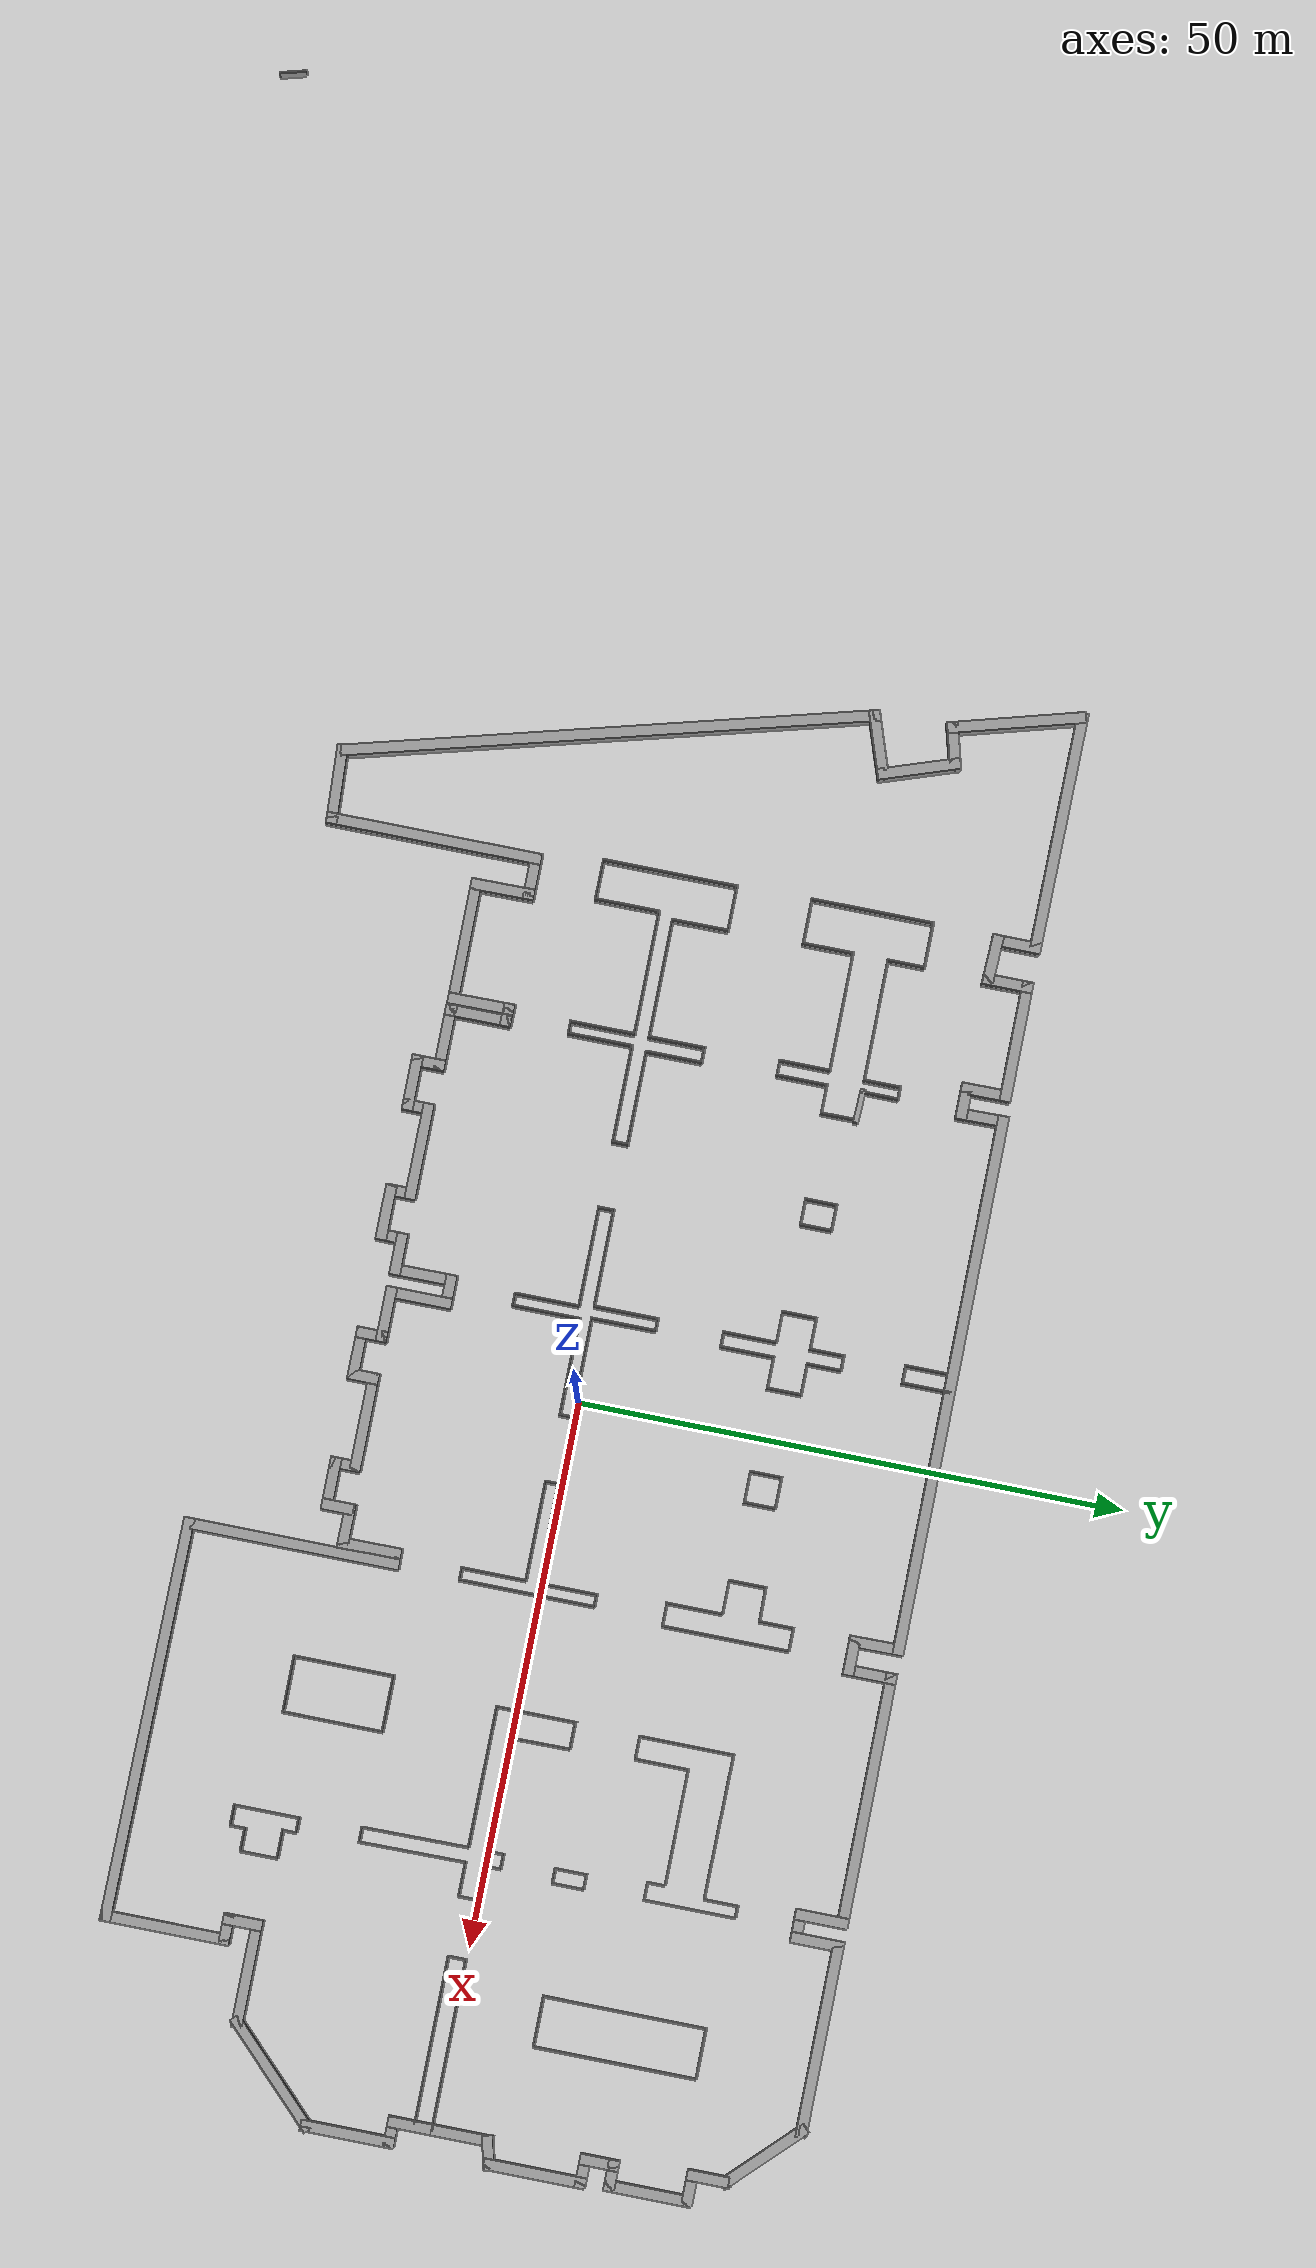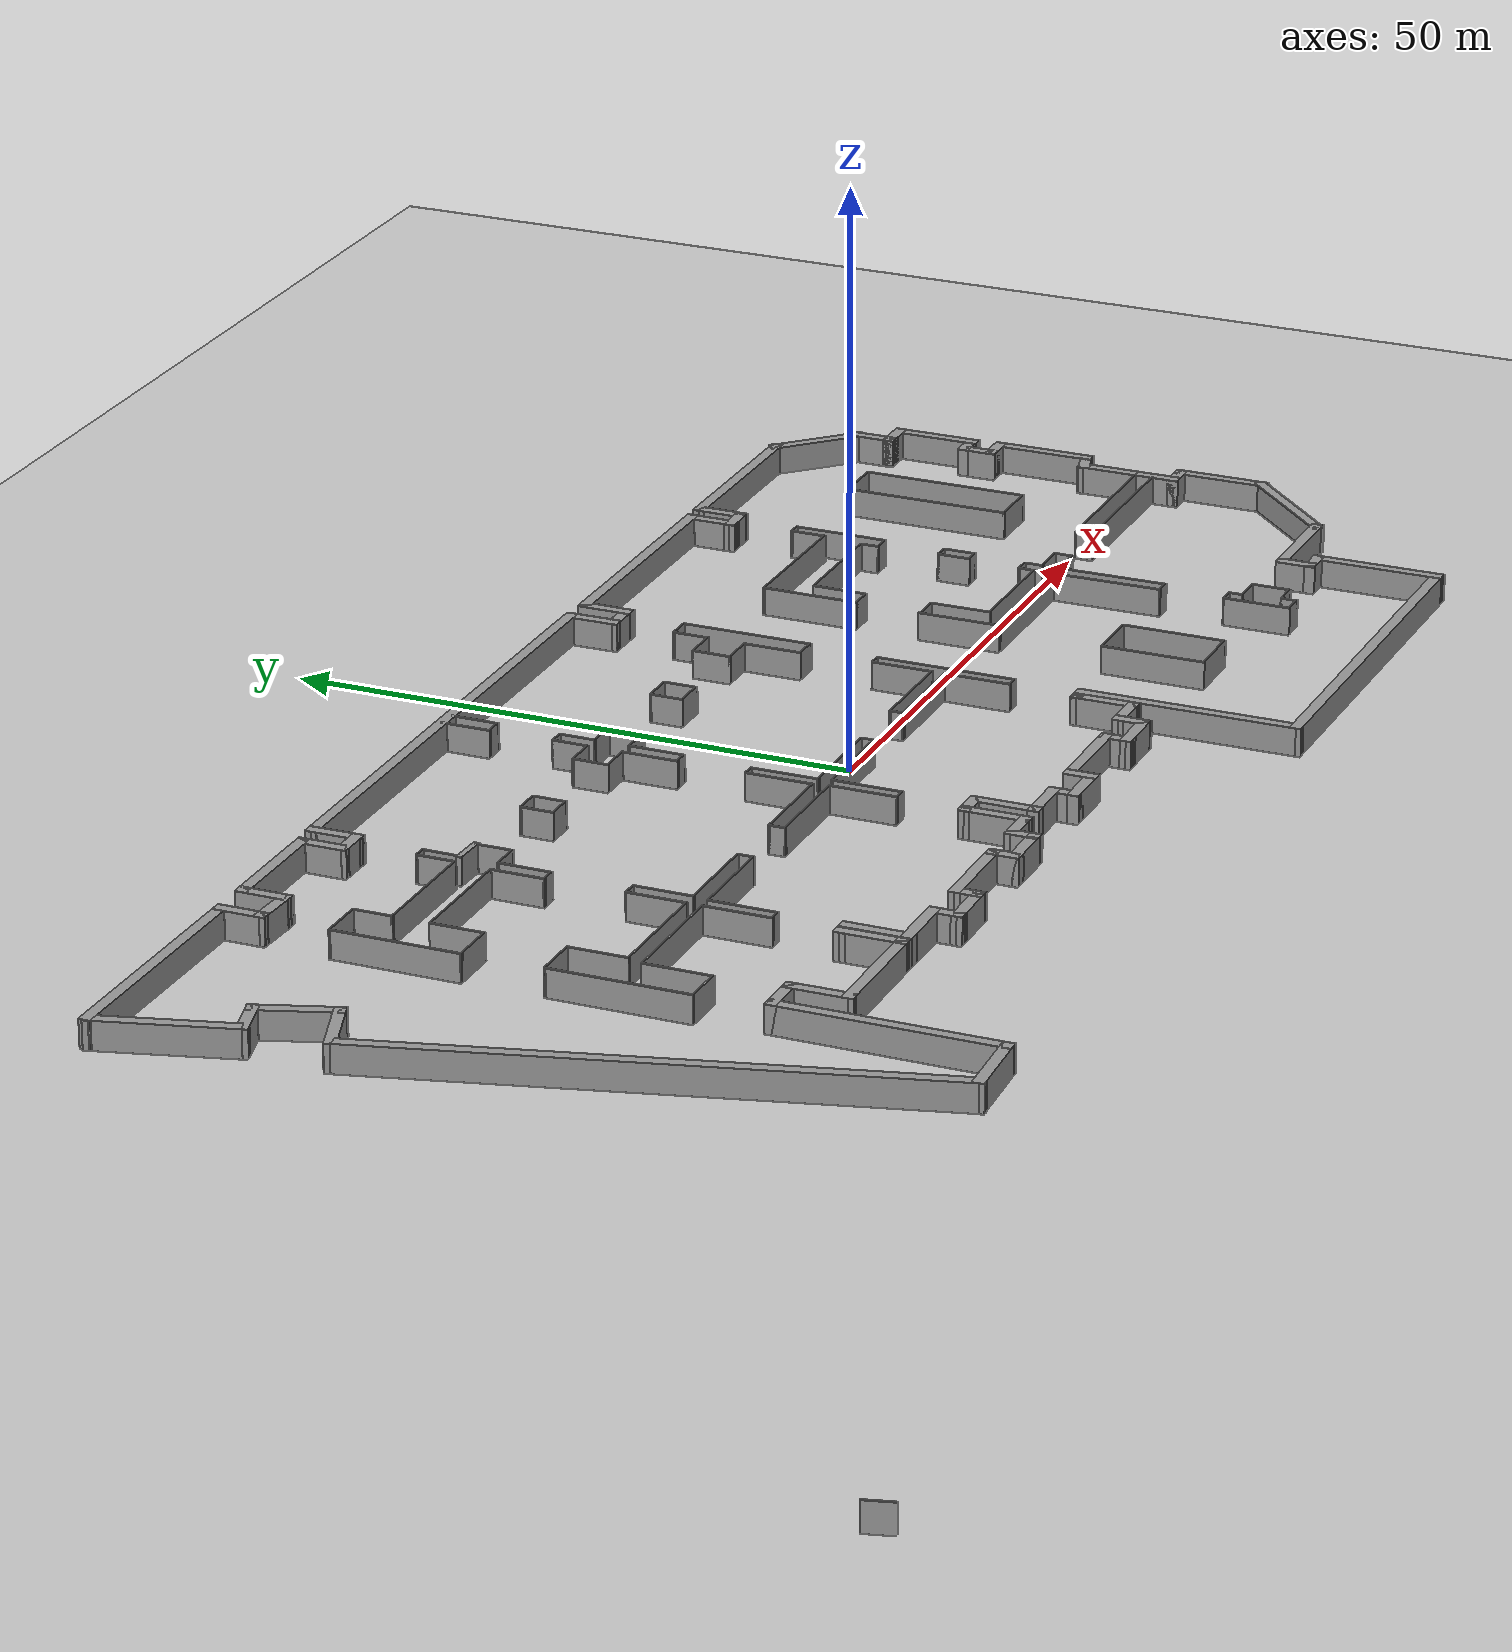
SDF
<sdf version="1.7">
 <world name="default">
  <light name="sun" type="directional">
   <pose>0 0 10 0 -0 0</pose>
   <diffuse>0.8 0.8 0.8 1</diffuse>
   <specular>0.2 0.2 0.2 1</specular>
   <attenuation>
    <range>1000</range>
    <constant>0.9</constant>
    <linear>0.01</linear>
    <quadratic>0.001</quadratic>
   </attenuation>
   <direction>-0.5 0.1 -0.9</direction>
   <spot><inner_angle>0</inner_angle><outer_angle>0</outer_angle><falloff>0</falloff></spot>
  </light>
  <model name="ground_plane">
   <static>1</static>
   <link name="link">
    <collision name="collision">
     <geometry><plane><normal>0 0 1</normal><size>100 100</size></plane></geometry>
     <surface><friction><ode><mu>100</mu><mu2>50</mu2></ode></friction></surface>
    </collision>
    <visual name="visual">
     <cast_shadows>0</cast_shadows>
     <geometry><plane><normal>0 0 1</normal><size>100 100</size></plane></geometry>
     <material>
      <script><uri>file://media/materials/scripts/gazebo.material</uri><name>Gazebo/Grey</name></script>
     </material>
    </visual>
   </link>
  </model>
  <gravity>0 0 -9.8</gravity>
  <magnetic_field>6e-06 2.3e-05 -4.2e-05</magnetic_field>
  <atmosphere type="adiabatic"/>
  <physics type="ode">
   <max_step_size>0.001</max_step_size>
   <real_time_factor>1</real_time_factor>
   <real_time_update_rate>1000</real_time_update_rate>
  </physics>
  <scene><ambient>0.4 0.4 0.4 1</ambient><background>0.7 0.7 0.7 1</background><shadows>1</shadows></scene>
  <spherical_coordinates>
   <surface_model>EARTH_WGS84</surface_model>
   <latitude_deg>0</latitude_deg>
   <longitude_deg>0</longitude_deg>
   <elevation>0</elevation>
   <heading_deg>0</heading_deg>
  </spherical_coordinates>
  <model name="map7">
   <pose>-22.5342 -8.78038 0 0 -0 0</pose>
   <link name="Wall_0">
    <collision name="Wall_0_Collision">
     <geometry><box><size>22.3381 1 2.5</size></box></geometry>
     <pose>0 0 1.25 0 -0 0</pose>
    </collision>
    <visual name="Wall_0_Visual">
     <pose>0 0 1.25 0 -0 0</pose>
     <geometry><box><size>22.3381 1 2.5</size></box></geometry>
     <material>
      <script><uri>file://media/materials/scripts/gazebo.material</uri><name>Gazebo/Grey</name></script>
      <ambient>1 1 1 1</ambient>
     </material>
     <meta><layer>0</layer></meta>
    </visual>
    <pose>-36.4768 41.2489 0 0 -0 -0.006983</pose>
   </link>
   <link name="Wall_1">
    <collision name="Wall_1_Collision">
     <geometry><box><size>4.5 1 2.5</size></box></geometry>
     <pose>0 0 1.25 0 -0 0</pose>
    </collision>
    <visual name="Wall_1_Visual">
     <pose>0 0 1.25 0 -0 0</pose>
     <geometry><box><size>4.5 1 2.5</size></box></geometry>
     <material>
      <script><uri>file://media/materials/scripts/gazebo.material</uri><name>Gazebo/Grey</name></script>
      <ambient>1 1 1 1</ambient>
     </material>
     <meta><layer>0</layer></meta>
    </visual>
    <pose>-25.8078 39.4244 0 0 -0 -1.5708</pose>
   </link>
   <link name="Wall_10">
    <collision name="Wall_10_Collision">
     <geometry><box><size>3.59994 1 2.5</size></box></geometry>
     <pose>0 0 1.25 0 -0 0</pose>
    </collision>
    <visual name="Wall_10_Visual">
     <pose>0 0 1.25 0 -0 0</pose>
     <geometry><box><size>3.59994 1 2.5</size></box></geometry>
     <material>
      <script><uri>file://media/materials/scripts/gazebo.material</uri><name>Gazebo/Grey</name></script>
      <ambient>1 1 1 1</ambient>
     </material>
     <meta><layer>0</layer></meta>
    </visual>
    <pose>40.1802 37.2854 0 0 -0 0</pose>
   </link>
   <link name="Wall_101">
    <collision name="Wall_101_Collision">
     <geometry><box><size>12.25 0.15 2.5</size></box></geometry>
     <pose>0 0 1.25 0 -0 0</pose>
    </collision>
    <visual name="Wall_101_Visual">
     <pose>0 0 1.25 0 -0 0</pose>
     <geometry><box><size>12.25 0.15 2.5</size></box></geometry>
     <material>
      <script><uri>file://media/materials/scripts/gazebo.material</uri><name>Gazebo/Grey</name></script>
      <ambient>1 1 1 1</ambient>
     </material>
     <meta><layer>0</layer></meta>
    </visual>
    <pose>-26.0311 7.38819 0 0 -0 -1.5708</pose>
   </link>
   <link name="Wall_102">
    <collision name="Wall_102_Collision">
     <geometry><box><size>3.77517 0.15 2.5</size></box></geometry>
     <pose>0 0 1.25 0 -0 0</pose>
    </collision>
    <visual name="Wall_102_Visual">
     <pose>0 0 1.25 0 -0 0</pose>
     <geometry><box><size>3.77517 0.15 2.5</size></box></geometry>
     <material>
      <script><uri>file://media/materials/scripts/gazebo.material</uri><name>Gazebo/Grey</name></script>
      <ambient>1 1 1 1</ambient>
     </material>
     <meta><layer>0</layer></meta>
    </visual>
    <pose>-24.2186 1.29268 0 0 -0 -0.005925</pose>
   </link>
   <link name="Wall_103">
    <collision name="Wall_103_Collision">
     <geometry><box><size>6 0.15 2.5</size></box></geometry>
     <pose>0 0 1.25 0 -0 0</pose>
    </collision>
    <visual name="Wall_103_Visual">
     <pose>0 0 1.25 0 -0 0</pose>
     <geometry><box><size>6 0.15 2.5</size></box></geometry>
     <material>
      <script><uri>file://media/materials/scripts/gazebo.material</uri><name>Gazebo/Grey</name></script>
      <ambient>1 1 1 1</ambient>
     </material>
     <meta><layer>0</layer></meta>
    </visual>
    <pose>-22.406 4.20694 0 0 -0 1.5708</pose>
   </link>
   <link name="Wall_104">
    <collision name="Wall_104_Collision">
     <geometry><box><size>11.5 0.15 2.5</size></box></geometry>
     <pose>0 0 1.25 0 -0 0</pose>
    </collision>
    <visual name="Wall_104_Visual">
     <pose>0 0 1.25 0 -0 0</pose>
     <geometry><box><size>11.5 0.15 2.5</size></box></geometry>
     <material>
      <script><uri>file://media/materials/scripts/gazebo.material</uri><name>Gazebo/Grey</name></script>
      <ambient>1 1 1 1</ambient>
     </material>
     <meta><layer>0</layer></meta>
    </visual>
    <pose>-16.731 7.13194 0 0 -0 0</pose>
   </link>
   <link name="Wall_105">
    <collision name="Wall_105_Collision">
     <geometry><box><size>6 0.15 2.5</size></box></geometry>
     <pose>0 0 1.25 0 -0 0</pose>
    </collision>
    <visual name="Wall_105_Visual">
     <pose>0 0 1.25 0 -0 0</pose>
     <geometry><box><size>6 0.15 2.5</size></box></geometry>
     <material>
      <script><uri>file://media/materials/scripts/gazebo.material</uri><name>Gazebo/Grey</name></script>
      <ambient>1 1 1 1</ambient>
     </material>
     <meta><layer>0</layer></meta>
    </visual>
    <pose>-11.056 4.20694 0 0 -0 -1.5708</pose>
   </link>
   <link name="Wall_106">
    <collision name="Wall_106_Collision">
     <geometry><box><size>1.25 0.15 2.5</size></box></geometry>
     <pose>0 0 1.25 0 -0 0</pose>
    </collision>
    <visual name="Wall_106_Visual">
     <pose>0 0 1.25 0 -0 0</pose>
     <geometry><box><size>1.25 0.15 2.5</size></box></geometry>
     <material>
      <script><uri>file://media/materials/scripts/gazebo.material</uri><name>Gazebo/Grey</name></script>
      <ambient>1 1 1 1</ambient>
     </material>
     <meta><layer>0</layer></meta>
    </visual>
    <pose>-10.506 1.28194 0 0 -0 0</pose>
   </link>
   <link name="Wall_107">
    <collision name="Wall_107_Collision">
     <geometry><box><size>6 0.15 2.5</size></box></geometry>
     <pose>0 0 1.25 0 -0 0</pose>
    </collision>
    <visual name="Wall_107_Visual">
     <pose>0 0 1.25 0 -0 0</pose>
     <geometry><box><size>6 0.15 2.5</size></box></geometry>
     <material>
      <script><uri>file://media/materials/scripts/gazebo.material</uri><name>Gazebo/Grey</name></script>
      <ambient>1 1 1 1</ambient>
     </material>
     <meta><layer>0</layer></meta>
    </visual>
    <pose>-9.95603 4.20694 0 0 -0 1.5708</pose>
   </link>
   <link name="Wall_108">
    <collision name="Wall_108_Collision">
     <geometry><box><size>9 0.15 2.5</size></box></geometry>
     <pose>0 0 1.25 0 -0 0</pose>
    </collision>
    <visual name="Wall_108_Visual">
     <pose>0 0 1.25 0 -0 0</pose>
     <geometry><box><size>9 0.15 2.5</size></box></geometry>
     <material>
      <script><uri>file://media/materials/scripts/gazebo.material</uri><name>Gazebo/Grey</name></script>
      <ambient>1 1 1 1</ambient>
     </material>
     <meta><layer>0</layer></meta>
    </visual>
    <pose>-5.53103 7.13194 0 0 -0 0</pose>
   </link>
   <link name="Wall_109">
    <collision name="Wall_109_Collision">
     <geometry><box><size>1.5 0.15 2.5</size></box></geometry>
     <pose>0 0 1.25 0 -0 0</pose>
    </collision>
    <visual name="Wall_109_Visual">
     <pose>0 0 1.25 0 -0 0</pose>
     <geometry><box><size>1.5 0.15 2.5</size></box></geometry>
     <material>
      <script><uri>file://media/materials/scripts/gazebo.material</uri><name>Gazebo/Grey</name></script>
      <ambient>1 1 1 1</ambient>
     </material>
     <meta><layer>0</layer></meta>
    </visual>
    <pose>-1.10603 7.80694 0 0 -0 1.5708</pose>
   </link>
   <link name="Wall_11">
    <collision name="Wall_11_Collision">
     <geometry><box><size>4.85041 1 2.5</size></box></geometry>
     <pose>0 0 1.25 0 -0 0</pose>
    </collision>
    <visual name="Wall_11_Visual">
     <pose>0 0 1.25 0 -0 0</pose>
     <geometry><box><size>4.85041 1 2.5</size></box></geometry>
     <material>
      <script><uri>file://media/materials/scripts/gazebo.material</uri><name>Gazebo/Grey</name></script>
      <ambient>1 1 1 1</ambient>
     </material>
     <meta><layer>0</layer></meta>
    </visual>
    <pose>41.4802 39.2104 0 0 -0 1.5708</pose>
   </link>
   <link name="Wall_110">
    <collision name="Wall_110_Collision">
     <geometry><box><size>8.75 0.15 2.5</size></box></geometry>
     <pose>0 0 1.25 0 -0 0</pose>
    </collision>
    <visual name="Wall_110_Visual">
     <pose>0 0 1.25 0 -0 0</pose>
     <geometry><box><size>8.75 0.15 2.5</size></box></geometry>
     <material>
      <script><uri>file://media/materials/scripts/gazebo.material</uri><name>Gazebo/Grey</name></script>
      <ambient>1 1 1 1</ambient>
     </material>
     <meta><layer>0</layer></meta>
    </visual>
    <pose>-5.40603 8.48194 0 0 -0 3.14159</pose>
   </link>
   <link name="Wall_111">
    <collision name="Wall_111_Collision">
     <geometry><box><size>5.25 0.15 2.5</size></box></geometry>
     <pose>0 0 1.25 0 -0 0</pose>
    </collision>
    <visual name="Wall_111_Visual">
     <pose>0 0 1.25 0 -0 0</pose>
     <geometry><box><size>5.25 0.15 2.5</size></box></geometry>
     <material>
      <script><uri>file://media/materials/scripts/gazebo.material</uri><name>Gazebo/Grey</name></script>
      <ambient>1 1 1 1</ambient>
     </material>
     <meta><layer>0</layer></meta>
    </visual>
    <pose>-9.70603 11.0319 0 0 -0 1.5708</pose>
   </link>
   <link name="Wall_112">
    <collision name="Wall_112_Collision">
     <geometry><box><size>1.5 0.15 2.5</size></box></geometry>
     <pose>0 0 1.25 0 -0 0</pose>
    </collision>
    <visual name="Wall_112_Visual">
     <pose>0 0 1.25 0 -0 0</pose>
     <geometry><box><size>1.5 0.15 2.5</size></box></geometry>
     <material>
      <script><uri>file://media/materials/scripts/gazebo.material</uri><name>Gazebo/Grey</name></script>
      <ambient>1 1 1 1</ambient>
     </material>
     <meta><layer>0</layer></meta>
    </visual>
    <pose>-10.381 13.5819 0 0 -0 3.14159</pose>
   </link>
   <link name="Wall_113">
    <collision name="Wall_113_Collision">
     <geometry><box><size>5.25 0.15 2.5</size></box></geometry>
     <pose>0 0 1.25 0 -0 0</pose>
    </collision>
    <visual name="Wall_113_Visual">
     <pose>0 0 1.25 0 -0 0</pose>
     <geometry><box><size>5.25 0.15 2.5</size></box></geometry>
     <material>
      <script><uri>file://media/materials/scripts/gazebo.material</uri><name>Gazebo/Grey</name></script>
      <ambient>1 1 1 1</ambient>
     </material>
     <meta><layer>0</layer></meta>
    </visual>
    <pose>-11.056 11.0319 0 0 -0 -1.5708</pose>
   </link>
   <link name="Wall_114">
    <collision name="Wall_114_Collision">
     <geometry><box><size>11 0.15 2.5</size></box></geometry>
     <pose>0 0 1.25 0 -0 0</pose>
    </collision>
    <visual name="Wall_114_Visual">
     <pose>0 0 1.25 0 -0 0</pose>
     <geometry><box><size>11 0.15 2.5</size></box></geometry>
     <material>
      <script><uri>file://media/materials/scripts/gazebo.material</uri><name>Gazebo/Grey</name></script>
      <ambient>1 1 1 1</ambient>
     </material>
     <meta><layer>0</layer></meta>
    </visual>
    <pose>-16.481 8.48194 0 0 -0 3.14159</pose>
   </link>
   <link name="Wall_115">
    <collision name="Wall_115_Collision">
     <geometry><box><size>5.26489 0.15 2.5</size></box></geometry>
     <pose>0 0 1.25 0 -0 0</pose>
    </collision>
    <visual name="Wall_115_Visual">
     <pose>0 0 1.25 0 -0 0</pose>
     <geometry><box><size>5.26489 0.15 2.5</size></box></geometry>
     <material>
      <script><uri>file://media/materials/scripts/gazebo.material</uri><name>Gazebo/Grey</name></script>
      <ambient>1 1 1 1</ambient>
     </material>
     <meta><layer>0</layer></meta>
    </visual>
    <pose>-21.9184 11.0394 0 0 -0 1.57563</pose>
   </link>
   <link name="Wall_116">
    <collision name="Wall_116_Collision">
     <geometry><box><size>4.25 0.15 2.5</size></box></geometry>
     <pose>0 0 1.25 0 -0 0</pose>
    </collision>
    <visual name="Wall_116_Visual">
     <pose>0 0 1.25 0 -0 0</pose>
     <geometry><box><size>4.25 0.15 2.5</size></box></geometry>
     <material>
      <script><uri>file://media/materials/scripts/gazebo.material</uri><name>Gazebo/Grey</name></script>
      <ambient>1 1 1 1</ambient>
     </material>
     <meta><layer>0</layer></meta>
    </visual>
    <pose>-23.9807 13.5918 0 0 -0 3.14159</pose>
   </link>
   <link name="Wall_118">
    <collision name="Wall_118_Collision">
     <geometry><box><size>9 0.15 2.5</size></box></geometry>
     <pose>0 0 1.25 0 -0 0</pose>
    </collision>
    <visual name="Wall_118_Visual">
     <pose>0 0 1.25 0 -0 0</pose>
     <geometry><box><size>9 0.15 2.5</size></box></geometry>
     <material>
      <script><uri>file://media/materials/scripts/gazebo.material</uri><name>Gazebo/Grey</name></script>
      <ambient>1 1 1 1</ambient>
     </material>
     <meta><layer>0</layer></meta>
    </visual>
    <pose>9.40506 8.40745 0 0 -0 0</pose>
   </link>
   <link name="Wall_119">
    <collision name="Wall_119_Collision">
     <geometry><box><size>6 0.15 2.5</size></box></geometry>
     <pose>0 0 1.25 0 -0 0</pose>
    </collision>
    <visual name="Wall_119_Visual">
     <pose>0 0 1.25 0 -0 0</pose>
     <geometry><box><size>6 0.15 2.5</size></box></geometry>
     <material>
      <script><uri>file://media/materials/scripts/gazebo.material</uri><name>Gazebo/Grey</name></script>
      <ambient>1 1 1 1</ambient>
     </material>
     <meta><layer>0</layer></meta>
    </visual>
    <pose>13.8301 11.3324 0 0 -0 1.5708</pose>
   </link>
   <link name="Wall_12">
    <collision name="Wall_12_Collision">
     <geometry><box><size>23.3499 1 2.5</size></box></geometry>
     <pose>0 0 1.25 0 -0 0</pose>
    </collision>
    <visual name="Wall_12_Visual">
     <pose>0 0 1.25 0 -0 0</pose>
     <geometry><box><size>23.3499 1 2.5</size></box></geometry>
     <material>
      <script><uri>file://media/materials/scripts/gazebo.material</uri><name>Gazebo/Grey</name></script>
      <ambient>1 1 1 1</ambient>
     </material>
     <meta><layer>0</layer></meta>
    </visual>
    <pose>52.6552 41.1354 0 0 -0 0</pose>
   </link>
   <link name="Wall_120">
    <collision name="Wall_120_Collision">
     <geometry><box><size>1.25 0.15 2.5</size></box></geometry>
     <pose>0 0 1.25 0 -0 0</pose>
    </collision>
    <visual name="Wall_120_Visual">
     <pose>0 0 1.25 0 -0 0</pose>
     <geometry><box><size>1.25 0.15 2.5</size></box></geometry>
     <material>
      <script><uri>file://media/materials/scripts/gazebo.material</uri><name>Gazebo/Grey</name></script>
      <ambient>1 1 1 1</ambient>
     </material>
     <meta><layer>0</layer></meta>
    </visual>
    <pose>14.3801 14.2574 0 0 -0 0</pose>
   </link>
   <link name="Wall_121">
    <collision name="Wall_121_Collision">
     <geometry><box><size>6 0.15 2.5</size></box></geometry>
     <pose>0 0 1.25 0 -0 0</pose>
    </collision>
    <visual name="Wall_121_Visual">
     <pose>0 0 1.25 0 -0 0</pose>
     <geometry><box><size>6 0.15 2.5</size></box></geometry>
     <material>
      <script><uri>file://media/materials/scripts/gazebo.material</uri><name>Gazebo/Grey</name></script>
      <ambient>1 1 1 1</ambient>
     </material>
     <meta><layer>0</layer></meta>
    </visual>
    <pose>14.9301 11.3324 0 0 -0 -1.5708</pose>
   </link>
   <link name="Wall_122">
    <collision name="Wall_122_Collision">
     <geometry><box><size>9.25 0.15 2.5</size></box></geometry>
     <pose>0 0 1.25 0 -0 0</pose>
    </collision>
    <visual name="Wall_122_Visual">
     <pose>0 0 1.25 0 -0 0</pose>
     <geometry><box><size>9.25 0.15 2.5</size></box></geometry>
     <material>
      <script><uri>file://media/materials/scripts/gazebo.material</uri><name>Gazebo/Grey</name></script>
      <ambient>1 1 1 1</ambient>
     </material>
     <meta><layer>0</layer></meta>
    </visual>
    <pose>19.4801 8.40745 0 0 -0 0</pose>
   </link>
   <link name="Wall_123">
    <collision name="Wall_123_Collision">
     <geometry><box><size>1.25 0.15 2.5</size></box></geometry>
     <pose>0 0 1.25 0 -0 0</pose>
    </collision>
    <visual name="Wall_123_Visual">
     <pose>0 0 1.25 0 -0 0</pose>
     <geometry><box><size>1.25 0.15 2.5</size></box></geometry>
     <material>
      <script><uri>file://media/materials/scripts/gazebo.material</uri><name>Gazebo/Grey</name></script>
      <ambient>1 1 1 1</ambient>
     </material>
     <meta><layer>0</layer></meta>
    </visual>
    <pose>24.0301 7.85745 0 0 -0 -1.5708</pose>
   </link>
   <link name="Wall_124">
    <collision name="Wall_124_Collision">
     <geometry><box><size>9 0.15 2.5</size></box></geometry>
     <pose>0 0 1.25 0 -0 0</pose>
    </collision>
    <visual name="Wall_124_Visual">
     <pose>0 0 1.25 0 -0 0</pose>
     <geometry><box><size>9 0.15 2.5</size></box></geometry>
     <material>
      <script><uri>file://media/materials/scripts/gazebo.material</uri><name>Gazebo/Grey</name></script>
      <ambient>1 1 1 1</ambient>
     </material>
     <meta><layer>0</layer></meta>
    </visual>
    <pose>19.6051 7.30745 0 0 -0 3.14159</pose>
   </link>
   <link name="Wall_125">
    <collision name="Wall_125_Collision">
     <geometry><box><size>6.25 0.15 2.5</size></box></geometry>
     <pose>0 0 1.25 0 -0 0</pose>
    </collision>
    <visual name="Wall_125_Visual">
     <pose>0 0 1.25 0 -0 0</pose>
     <geometry><box><size>6.25 0.15 2.5</size></box></geometry>
     <material>
      <script><uri>file://media/materials/scripts/gazebo.material</uri><name>Gazebo/Grey</name></script>
      <ambient>1 1 1 1</ambient>
     </material>
     <meta><layer>0</layer></meta>
    </visual>
    <pose>15.1801 4.25745 0 0 -0 -1.5708</pose>
   </link>
   <link name="Wall_126">
    <collision name="Wall_126_Collision">
     <geometry><box><size>1.25 0.15 2.5</size></box></geometry>
     <pose>0 0 1.25 0 -0 0</pose>
    </collision>
    <visual name="Wall_126_Visual">
     <pose>0 0 1.25 0 -0 0</pose>
     <geometry><box><size>1.25 0.15 2.5</size></box></geometry>
     <material>
      <script><uri>file://media/materials/scripts/gazebo.material</uri><name>Gazebo/Grey</name></script>
      <ambient>1 1 1 1</ambient>
     </material>
     <meta><layer>0</layer></meta>
    </visual>
    <pose>14.6301 1.20745 0 0 -0 3.14159</pose>
   </link>
   <link name="Wall_127">
    <collision name="Wall_127_Collision">
     <geometry><box><size>6 0.15 2.5</size></box></geometry>
     <pose>0 0 1.25 0 -0 0</pose>
    </collision>
    <visual name="Wall_127_Visual">
     <pose>0 0 1.25 0 -0 0</pose>
     <geometry><box><size>6 0.15 2.5</size></box></geometry>
     <material>
      <script><uri>file://media/materials/scripts/gazebo.material</uri><name>Gazebo/Grey</name></script>
      <ambient>1 1 1 1</ambient>
     </material>
     <meta><layer>0</layer></meta>
    </visual>
    <pose>14.0801 4.13245 0 0 -0 1.5708</pose>
   </link>
   <link name="Wall_128">
    <collision name="Wall_128_Collision">
     <geometry><box><size>9.25 0.15 2.5</size></box></geometry>
     <pose>0 0 1.25 0 -0 0</pose>
    </collision>
    <visual name="Wall_128_Visual">
     <pose>0 0 1.25 0 -0 0</pose>
     <geometry><box><size>9.25 0.15 2.5</size></box></geometry>
     <material>
      <script><uri>file://media/materials/scripts/gazebo.material</uri><name>Gazebo/Grey</name></script>
      <ambient>1 1 1 1</ambient>
     </material>
     <meta><layer>0</layer></meta>
    </visual>
    <pose>9.53006 7.05745 0 0 -0 3.14159</pose>
   </link>
   <link name="Wall_129">
    <collision name="Wall_129_Collision">
     <geometry><box><size>1.5 0.15 2.5</size></box></geometry>
     <pose>0 0 1.25 0 -0 0</pose>
    </collision>
    <visual name="Wall_129_Visual">
     <pose>0 0 1.25 0 -0 0</pose>
     <geometry><box><size>1.5 0.15 2.5</size></box></geometry>
     <material>
      <script><uri>file://media/materials/scripts/gazebo.material</uri><name>Gazebo/Grey</name></script>
      <ambient>1 1 1 1</ambient>
     </material>
     <meta><layer>0</layer></meta>
    </visual>
    <pose>4.98006 7.73245 0 0 -0 1.5708</pose>
   </link>
   <link name="Wall_13">
    <collision name="Wall_13_Collision">
     <geometry><box><size>4.84959 1 2.5</size></box></geometry>
     <pose>0 0 1.25 0 -0 0</pose>
    </collision>
    <visual name="Wall_13_Visual">
     <pose>0 0 1.25 0 -0 0</pose>
     <geometry><box><size>4.84959 1 2.5</size></box></geometry>
     <material>
      <script><uri>file://media/materials/scripts/gazebo.material</uri><name>Gazebo/Grey</name></script>
      <ambient>1 1 1 1</ambient>
     </material>
     <meta><layer>0</layer></meta>
    </visual>
    <pose>63.8302 39.2104 0 0 -0 -1.5708</pose>
   </link>
   <link name="Wall_131">
    <collision name="Wall_131_Collision">
     <geometry><box><size>9.25 0.15 2.5</size></box></geometry>
     <pose>0 0 1.25 0 -0 0</pose>
    </collision>
    <visual name="Wall_131_Visual">
     <pose>0 0 1.25 0 -0 0</pose>
     <geometry><box><size>9.25 0.15 2.5</size></box></geometry>
     <material>
      <script><uri>file://media/materials/scripts/gazebo.material</uri><name>Gazebo/Grey</name></script>
      <ambient>1 1 1 1</ambient>
     </material>
     <meta><layer>0</layer></meta>
    </visual>
    <pose>34.7213 8.36981 0 0 -0 0</pose>
   </link>
   <link name="Wall_132">
    <collision name="Wall_132_Collision">
     <geometry><box><size>5.5 0.15 2.5</size></box></geometry>
     <pose>0 0 1.25 0 -0 0</pose>
    </collision>
    <visual name="Wall_132_Visual">
     <pose>0 0 1.25 0 -0 0</pose>
     <geometry><box><size>5.5 0.15 2.5</size></box></geometry>
     <material>
      <script><uri>file://media/materials/scripts/gazebo.material</uri><name>Gazebo/Grey</name></script>
      <ambient>1 1 1 1</ambient>
     </material>
     <meta><layer>0</layer></meta>
    </visual>
    <pose>39.2713 11.0448 0 0 -0 1.5708</pose>
   </link>
   <link name="Wall_133">
    <collision name="Wall_133_Collision">
     <geometry><box><size>1.25 0.15 2.5</size></box></geometry>
     <pose>0 0 1.25 0 -0 0</pose>
    </collision>
    <visual name="Wall_133_Visual">
     <pose>0 0 1.25 0 -0 0</pose>
     <geometry><box><size>1.25 0.15 2.5</size></box></geometry>
     <material>
      <script><uri>file://media/materials/scripts/gazebo.material</uri><name>Gazebo/Grey</name></script>
      <ambient>1 1 1 1</ambient>
     </material>
     <meta><layer>0</layer></meta>
    </visual>
    <pose>39.8213 13.7198 0 0 -0 0</pose>
   </link>
   <link name="Wall_134">
    <collision name="Wall_134_Collision">
     <geometry><box><size>12.5 0.15 2.5</size></box></geometry>
     <pose>0 0 1.25 0 -0 0</pose>
    </collision>
    <visual name="Wall_134_Visual">
     <pose>0 0 1.25 0 -0 0</pose>
     <geometry><box><size>12.5 0.15 2.5</size></box></geometry>
     <material>
      <script><uri>file://media/materials/scripts/gazebo.material</uri><name>Gazebo/Grey</name></script>
      <ambient>1 1 1 1</ambient>
     </material>
     <meta><layer>0</layer></meta>
    </visual>
    <pose>40.3713 7.54481 0 0 -0 -1.5708</pose>
   </link>
   <link name="Wall_135">
    <collision name="Wall_135_Collision">
     <geometry><box><size>1.25 0.15 2.5</size></box></geometry>
     <pose>0 0 1.25 0 -0 0</pose>
    </collision>
    <visual name="Wall_135_Visual">
     <pose>0 0 1.25 0 -0 0</pose>
     <geometry><box><size>1.25 0.15 2.5</size></box></geometry>
     <material>
      <script><uri>file://media/materials/scripts/gazebo.material</uri><name>Gazebo/Grey</name></script>
      <ambient>1 1 1 1</ambient>
     </material>
     <meta><layer>0</layer></meta>
    </visual>
    <pose>39.8213 1.36981 0 0 -0 3.14159</pose>
   </link>
   <link name="Wall_136">
    <collision name="Wall_136_Collision">
     <geometry><box><size>6 0.15 2.5</size></box></geometry>
     <pose>0 0 1.25 0 -0 0</pose>
    </collision>
    <visual name="Wall_136_Visual">
     <pose>0 0 1.25 0 -0 0</pose>
     <geometry><box><size>6 0.15 2.5</size></box></geometry>
     <material>
      <script><uri>file://media/materials/scripts/gazebo.material</uri><name>Gazebo/Grey</name></script>
      <ambient>1 1 1 1</ambient>
     </material>
     <meta><layer>0</layer></meta>
    </visual>
    <pose>39.2713 4.29481 0 0 -0 1.5708</pose>
   </link>
   <link name="Wall_137">
    <collision name="Wall_137_Collision">
     <geometry><box><size>9.25 0.15 2.5</size></box></geometry>
     <pose>0 0 1.25 0 -0 0</pose>
    </collision>
    <visual name="Wall_137_Visual">
     <pose>0 0 1.25 0 -0 0</pose>
     <geometry><box><size>9.25 0.15 2.5</size></box></geometry>
     <material>
      <script><uri>file://media/materials/scripts/gazebo.material</uri><name>Gazebo/Grey</name></script>
      <ambient>1 1 1 1</ambient>
     </material>
     <meta><layer>0</layer></meta>
    </visual>
    <pose>34.7213 7.21981 0 0 -0 3.14159</pose>
   </link>
   <link name="Wall_138">
    <collision name="Wall_138_Collision">
     <geometry><box><size>1.25 0.15 2.5</size></box></geometry>
     <pose>0 0 1.25 0 -0 0</pose>
    </collision>
    <visual name="Wall_138_Visual">
     <pose>0 0 1.25 0 -0 0</pose>
     <geometry><box><size>1.25 0.15 2.5</size></box></geometry>
     <material>
      <script><uri>file://media/materials/scripts/gazebo.material</uri><name>Gazebo/Grey</name></script>
      <ambient>1 1 1 1</ambient>
     </material>
     <meta><layer>0</layer></meta>
    </visual>
    <pose>30.1713 7.76981 0 0 -0 1.5708</pose>
   </link>
   <link name="Wall_14">
    <collision name="Wall_14_Collision">
     <geometry><box><size>3.09994 1 2.5</size></box></geometry>
     <pose>0 0 1.25 0 -0 0</pose>
    </collision>
    <visual name="Wall_14_Visual">
     <pose>0 0 1.25 0 -0 0</pose>
     <geometry><box><size>3.09994 1 2.5</size></box></geometry>
     <material>
      <script><uri>file://media/materials/scripts/gazebo.material</uri><name>Gazebo/Grey</name></script>
      <ambient>1 1 1 1</ambient>
     </material>
     <meta><layer>0</layer></meta>
    </visual>
    <pose>64.8802 37.2949 0 0 -0 0.009047</pose>
   </link>
   <link name="Wall_140">
    <collision name="Wall_140_Collision">
     <geometry><box><size>3 0.15 2.5</size></box></geometry>
     <pose>0 0 1.25 0 -0 0</pose>
    </collision>
    <visual name="Wall_140_Visual">
     <pose>0 0 1.25 0 -0 0</pose>
     <geometry><box><size>3 0.15 2.5</size></box></geometry>
     <material>
      <script><uri>file://media/materials/scripts/gazebo.material</uri><name>Gazebo/Grey</name></script>
      <ambient>1 1 1 1</ambient>
     </material>
     <meta><layer>0</layer></meta>
    </visual>
    <pose>0.597433 26.6458 0 0 -0 -1.5708</pose>
   </link>
   <link name="Wall_141">
    <collision name="Wall_141_Collision">
     <geometry><box><size>2.5 0.15 2.5</size></box></geometry>
     <pose>0 0 1.25 0 -0 0</pose>
    </collision>
    <visual name="Wall_141_Visual">
     <pose>0 0 1.25 0 -0 0</pose>
     <geometry><box><size>2.5 0.15 2.5</size></box></geometry>
     <material>
      <script><uri>file://media/materials/scripts/gazebo.material</uri><name>Gazebo/Grey</name></script>
      <ambient>1 1 1 1</ambient>
     </material>
     <meta><layer>0</layer></meta>
    </visual>
    <pose>1.77243 25.2208 0 0 -0 0</pose>
   </link>
   <link name="Wall_142">
    <collision name="Wall_142_Collision">
     <geometry><box><size>3 0.15 2.5</size></box></geometry>
     <pose>0 0 1.25 0 -0 0</pose>
    </collision>
    <visual name="Wall_142_Visual">
     <pose>0 0 1.25 0 -0 0</pose>
     <geometry><box><size>3 0.15 2.5</size></box></geometry>
     <material>
      <script><uri>file://media/materials/scripts/gazebo.material</uri><name>Gazebo/Grey</name></script>
      <ambient>1 1 1 1</ambient>
     </material>
     <meta><layer>0</layer></meta>
    </visual>
    <pose>2.94743 26.6458 0 0 -0 1.5708</pose>
   </link>
   <link name="Wall_143">
    <collision name="Wall_143_Collision">
     <geometry><box><size>2.5 0.15 2.5</size></box></geometry>
     <pose>0 0 1.25 0 -0 0</pose>
    </collision>
    <visual name="Wall_143_Visual">
     <pose>0 0 1.25 0 -0 0</pose>
     <geometry><box><size>2.5 0.15 2.5</size></box></geometry>
     <material>
      <script><uri>file://media/materials/scripts/gazebo.material</uri><name>Gazebo/Grey</name></script>
      <ambient>1 1 1 1</ambient>
     </material>
     <meta><layer>0</layer></meta>
    </visual>
    <pose>1.77243 28.0708 0 0 -0 3.14159</pose>
   </link>
   <link name="Wall_145">
    <collision name="Wall_145_Collision">
     <geometry><box><size>3.25 0.15 2.5</size></box></geometry>
     <pose>0 0 1.25 0 -0 0</pose>
    </collision>
    <visual name="Wall_145_Visual">
     <pose>0 0 1.25 0 -0 0</pose>
     <geometry><box><size>3.25 0.15 2.5</size></box></geometry>
     <material>
      <script><uri>file://media/materials/scripts/gazebo.material</uri><name>Gazebo/Grey</name></script>
      <ambient>1 1 1 1</ambient>
     </material>
     <meta><layer>0</layer></meta>
    </visual>
    <pose>10.9844 26.7139 0 0 -0 -1.5708</pose>
   </link>
   <link name="Wall_146">
    <collision name="Wall_146_Collision">
     <geometry><box><size>3 0.15 2.5</size></box></geometry>
     <pose>0 0 1.25 0 -0 0</pose>
    </collision>
    <visual name="Wall_146_Visual">
     <pose>0 0 1.25 0 -0 0</pose>
     <geometry><box><size>3 0.15 2.5</size></box></geometry>
     <material>
      <script><uri>file://media/materials/scripts/gazebo.material</uri><name>Gazebo/Grey</name></script>
      <ambient>1 1 1 1</ambient>
     </material>
     <meta><layer>0</layer></meta>
    </visual>
    <pose>12.4094 25.1639 0 0 -0 0</pose>
   </link>
   <link name="Wall_147">
    <collision name="Wall_147_Collision">
     <geometry><box><size>5 0.15 2.5</size></box></geometry>
     <pose>0 0 1.25 0 -0 0</pose>
    </collision>
    <visual name="Wall_147_Visual">
     <pose>0 0 1.25 0 -0 0</pose>
     <geometry><box><size>5 0.15 2.5</size></box></geometry>
     <material>
      <script><uri>file://media/materials/scripts/gazebo.material</uri><name>Gazebo/Grey</name></script>
      <ambient>1 1 1 1</ambient>
     </material>
     <meta><layer>0</layer></meta>
    </visual>
    <pose>13.8344 22.7389 0 0 -0 -1.5708</pose>
   </link>
   <link name="Wall_148">
    <collision name="Wall_148_Collision">
     <geometry><box><size>1.5 0.15 2.5</size></box></geometry>
     <pose>0 0 1.25 0 -0 0</pose>
    </collision>
    <visual name="Wall_148_Visual">
     <pose>0 0 1.25 0 -0 0</pose>
     <geometry><box><size>1.5 0.15 2.5</size></box></geometry>
     <material>
      <script><uri>file://media/materials/scripts/gazebo.material</uri><name>Gazebo/Grey</name></script>
      <ambient>1 1 1 1</ambient>
     </material>
     <meta><layer>0</layer></meta>
    </visual>
    <pose>14.5094 20.3139 0 0 -0 0</pose>
   </link>
   <link name="Wall_149">
    <collision name="Wall_149_Collision">
     <geometry><box><size>5 0.15 2.5</size></box></geometry>
     <pose>0 0 1.25 0 -0 0</pose>
    </collision>
    <visual name="Wall_149_Visual">
     <pose>0 0 1.25 0 -0 0</pose>
     <geometry><box><size>5 0.15 2.5</size></box></geometry>
     <material>
      <script><uri>file://media/materials/scripts/gazebo.material</uri><name>Gazebo/Grey</name></script>
      <ambient>1 1 1 1</ambient>
     </material>
     <meta><layer>0</layer></meta>
    </visual>
    <pose>15.1844 22.7389 0 0 -0 1.5708</pose>
   </link>
   <link name="Wall_15">
    <collision name="Wall_15_Collision">
     <geometry><box><size>4.85064 1 2.5</size></box></geometry>
     <pose>0 0 1.25 0 -0 0</pose>
    </collision>
    <visual name="Wall_15_Visual">
     <pose>0 0 1.25 0 -0 0</pose>
     <geometry><box><size>4.85064 1 2.5</size></box></geometry>
     <material>
      <script><uri>file://media/materials/scripts/gazebo.material</uri><name>Gazebo/Grey</name></script>
      <ambient>1 1 1 1</ambient>
     </material>
     <meta><layer>0</layer></meta>
    </visual>
    <pose>65.9302 39.2299 0 0 -0 1.5708</pose>
   </link>
   <link name="Wall_150">
    <collision name="Wall_150_Collision">
     <geometry><box><size>3 0.15 2.5</size></box></geometry>
     <pose>0 0 1.25 0 -0 0</pose>
    </collision>
    <visual name="Wall_150_Visual">
     <pose>0 0 1.25 0 -0 0</pose>
     <geometry><box><size>3 0.15 2.5</size></box></geometry>
     <material>
      <script><uri>file://media/materials/scripts/gazebo.material</uri><name>Gazebo/Grey</name></script>
      <ambient>1 1 1 1</ambient>
     </material>
     <meta><layer>0</layer></meta>
    </visual>
    <pose>16.6094 25.1639 0 0 -0 0</pose>
   </link>
   <link name="Wall_151">
    <collision name="Wall_151_Collision">
     <geometry><box><size>3.25 0.15 2.5</size></box></geometry>
     <pose>0 0 1.25 0 -0 0</pose>
    </collision>
    <visual name="Wall_151_Visual">
     <pose>0 0 1.25 0 -0 0</pose>
     <geometry><box><size>3.25 0.15 2.5</size></box></geometry>
     <material>
      <script><uri>file://media/materials/scripts/gazebo.material</uri><name>Gazebo/Grey</name></script>
      <ambient>1 1 1 1</ambient>
     </material>
     <meta><layer>0</layer></meta>
    </visual>
    <pose>18.0344 26.7139 0 0 -0 1.5708</pose>
   </link>
   <link name="Wall_152">
    <collision name="Wall_152_Collision">
     <geometry><box><size>3 0.15 2.5</size></box></geometry>
     <pose>0 0 1.25 0 -0 0</pose>
    </collision>
    <visual name="Wall_152_Visual">
     <pose>0 0 1.25 0 -0 0</pose>
     <geometry><box><size>3 0.15 2.5</size></box></geometry>
     <material>
      <script><uri>file://media/materials/scripts/gazebo.material</uri><name>Gazebo/Grey</name></script>
      <ambient>1 1 1 1</ambient>
     </material>
     <meta><layer>0</layer></meta>
    </visual>
    <pose>16.6094 28.2639 0 0 -0 3.14159</pose>
   </link>
   <link name="Wall_153">
    <collision name="Wall_153_Collision">
     <geometry><box><size>3.25 0.15 2.5</size></box></geometry>
     <pose>0 0 1.25 0 -0 0</pose>
    </collision>
    <visual name="Wall_153_Visual">
     <pose>0 0 1.25 0 -0 0</pose>
     <geometry><box><size>3.25 0.15 2.5</size></box></geometry>
     <material>
      <script><uri>file://media/materials/scripts/gazebo.material</uri><name>Gazebo/Grey</name></script>
      <ambient>1 1 1 1</ambient>
     </material>
     <meta><layer>0</layer></meta>
    </visual>
    <pose>15.1844 29.8139 0 0 -0 1.5708</pose>
   </link>
   <link name="Wall_154">
    <collision name="Wall_154_Collision">
     <geometry><box><size>1.5 0.15 2.5</size></box></geometry>
     <pose>0 0 1.25 0 -0 0</pose>
    </collision>
    <visual name="Wall_154_Visual">
     <pose>0 0 1.25 0 -0 0</pose>
     <geometry><box><size>1.5 0.15 2.5</size></box></geometry>
     <material>
      <script><uri>file://media/materials/scripts/gazebo.material</uri><name>Gazebo/Grey</name></script>
      <ambient>1 1 1 1</ambient>
     </material>
     <meta><layer>0</layer></meta>
    </visual>
    <pose>14.5094 31.3639 0 0 -0 3.14159</pose>
   </link>
   <link name="Wall_155">
    <collision name="Wall_155_Collision">
     <geometry><box><size>3.25 0.15 2.5</size></box></geometry>
     <pose>0 0 1.25 0 -0 0</pose>
    </collision>
    <visual name="Wall_155_Visual">
     <pose>0 0 1.25 0 -0 0</pose>
     <geometry><box><size>3.25 0.15 2.5</size></box></geometry>
     <material>
      <script><uri>file://media/materials/scripts/gazebo.material</uri><name>Gazebo/Grey</name></script>
      <ambient>1 1 1 1</ambient>
     </material>
     <meta><layer>0</layer></meta>
    </visual>
    <pose>13.8344 29.8139 0 0 -0 -1.5708</pose>
   </link>
   <link name="Wall_157">
    <collision name="Wall_157_Collision">
     <geometry><box><size>3 0.15 2.5</size></box></geometry>
     <pose>0 0 1.25 0 -0 0</pose>
    </collision>
    <visual name="Wall_157_Visual">
     <pose>0 0 1.25 0 -0 0</pose>
     <geometry><box><size>3 0.15 2.5</size></box></geometry>
     <material>
      <script><uri>file://media/materials/scripts/gazebo.material</uri><name>Gazebo/Grey</name></script>
      <ambient>1 1 1 1</ambient>
     </material>
     <meta><layer>0</layer></meta>
    </visual>
    <pose>25.6969 26.5543 0 0 -0 -1.5708</pose>
   </link>
   <link name="Wall_158">
    <collision name="Wall_158_Collision">
     <geometry><box><size>3 0.15 2.5</size></box></geometry>
     <pose>0 0 1.25 0 -0 0</pose>
    </collision>
    <visual name="Wall_158_Visual">
     <pose>0 0 1.25 0 -0 0</pose>
     <geometry><box><size>3 0.15 2.5</size></box></geometry>
     <material>
      <script><uri>file://media/materials/scripts/gazebo.material</uri><name>Gazebo/Grey</name></script>
      <ambient>1 1 1 1</ambient>
     </material>
     <meta><layer>0</layer></meta>
    </visual>
    <pose>27.1219 25.1293 0 0 -0 0</pose>
   </link>
   <link name="Wall_159">
    <collision name="Wall_159_Collision">
     <geometry><box><size>3 0.15 2.5</size></box></geometry>
     <pose>0 0 1.25 0 -0 0</pose>
    </collision>
    <visual name="Wall_159_Visual">
     <pose>0 0 1.25 0 -0 0</pose>
     <geometry><box><size>3 0.15 2.5</size></box></geometry>
     <material>
      <script><uri>file://media/materials/scripts/gazebo.material</uri><name>Gazebo/Grey</name></script>
      <ambient>1 1 1 1</ambient>
     </material>
     <meta><layer>0</layer></meta>
    </visual>
    <pose>28.5469 26.5543 0 0 -0 1.5708</pose>
   </link>
   <link name="Wall_16">
    <collision name="Wall_16_Collision">
     <geometry><box><size>17.85 1 2.5</size></box></geometry>
     <pose>0 0 1.25 0 -0 0</pose>
    </collision>
    <visual name="Wall_16_Visual">
     <pose>0 0 1.25 0 -0 0</pose>
     <geometry><box><size>17.85 1 2.5</size></box></geometry>
     <material>
      <script><uri>file://media/materials/scripts/gazebo.material</uri><name>Gazebo/Grey</name></script>
      <ambient>1 1 1 1</ambient>
     </material>
     <meta><layer>0</layer></meta>
    </visual>
    <pose>74.3552 41.1454 0 0 -0 -0.001187</pose>
   </link>
   <link name="Wall_160">
    <collision name="Wall_160_Collision">
     <geometry><box><size>3 0.15 2.5</size></box></geometry>
     <pose>0 0 1.25 0 -0 0</pose>
    </collision>
    <visual name="Wall_160_Visual">
     <pose>0 0 1.25 0 -0 0</pose>
     <geometry><box><size>3 0.15 2.5</size></box></geometry>
     <material>
      <script><uri>file://media/materials/scripts/gazebo.material</uri><name>Gazebo/Grey</name></script>
      <ambient>1 1 1 1</ambient>
     </material>
     <meta><layer>0</layer></meta>
    </visual>
    <pose>27.1219 27.9793 0 0 -0 3.14159</pose>
   </link>
   <link name="Wall_162">
    <collision name="Wall_162_Collision">
     <geometry><box><size>3.5 0.15 2.5</size></box></geometry>
     <pose>0 0 1.25 0 -0 0</pose>
    </collision>
    <visual name="Wall_162_Visual">
     <pose>0 0 1.25 0 -0 0</pose>
     <geometry><box><size>3.5 0.15 2.5</size></box></geometry>
     <material>
      <script><uri>file://media/materials/scripts/gazebo.material</uri><name>Gazebo/Grey</name></script>
      <ambient>1 1 1 1</ambient>
     </material>
     <meta><layer>0</layer></meta>
    </visual>
    <pose>35.6855 26.845 0 0 -0 -1.5708</pose>
   </link>
   <link name="Wall_163">
    <collision name="Wall_163_Collision">
     <geometry><box><size>3.25 0.15 2.5</size></box></geometry>
     <pose>0 0 1.25 0 -0 0</pose>
    </collision>
    <visual name="Wall_163_Visual">
     <pose>0 0 1.25 0 -0 0</pose>
     <geometry><box><size>3.25 0.15 2.5</size></box></geometry>
     <material>
      <script><uri>file://media/materials/scripts/gazebo.material</uri><name>Gazebo/Grey</name></script>
      <ambient>1 1 1 1</ambient>
     </material>
     <meta><layer>0</layer></meta>
    </visual>
    <pose>37.2355 25.17 0 0 -0 0</pose>
   </link>
   <link name="Wall_164">
    <collision name="Wall_164_Collision">
     <geometry><box><size>5.25 0.15 2.5</size></box></geometry>
     <pose>0 0 1.25 0 -0 0</pose>
    </collision>
    <visual name="Wall_164_Visual">
     <pose>0 0 1.25 0 -0 0</pose>
     <geometry><box><size>5.25 0.15 2.5</size></box></geometry>
     <material>
      <script><uri>file://media/materials/scripts/gazebo.material</uri><name>Gazebo/Grey</name></script>
      <ambient>1 1 1 1</ambient>
     </material>
     <meta><layer>0</layer></meta>
    </visual>
    <pose>38.7855 22.62 0 0 -0 -1.5708</pose>
   </link>
   <link name="Wall_165">
    <collision name="Wall_165_Collision">
     <geometry><box><size>2.25 0.15 2.5</size></box></geometry>
     <pose>0 0 1.25 0 -0 0</pose>
    </collision>
    <visual name="Wall_165_Visual">
     <pose>0 0 1.25 0 -0 0</pose>
     <geometry><box><size>2.25 0.15 2.5</size></box></geometry>
     <material>
      <script><uri>file://media/materials/scripts/gazebo.material</uri><name>Gazebo/Grey</name></script>
      <ambient>1 1 1 1</ambient>
     </material>
     <meta><layer>0</layer></meta>
    </visual>
    <pose>39.8355 20.07 0 0 -0 0</pose>
   </link>
   <link name="Wall_166">
    <collision name="Wall_166_Collision">
     <geometry><box><size>11.75 0.15 2.5</size></box></geometry>
     <pose>0 0 1.25 0 -0 0</pose>
    </collision>
    <visual name="Wall_166_Visual">
     <pose>0 0 1.25 0 -0 0</pose>
     <geometry><box><size>11.75 0.15 2.5</size></box></geometry>
     <material>
      <script><uri>file://media/materials/scripts/gazebo.material</uri><name>Gazebo/Grey</name></script>
      <ambient>1 1 1 1</ambient>
     </material>
     <meta><layer>0</layer></meta>
    </visual>
    <pose>40.8855 25.87 0 0 -0 1.5708</pose>
   </link>
   <link name="Wall_167">
    <collision name="Wall_167_Collision">
     <geometry><box><size>2.25 0.15 2.5</size></box></geometry>
     <pose>0 0 1.25 0 -0 0</pose>
    </collision>
    <visual name="Wall_167_Visual">
     <pose>0 0 1.25 0 -0 0</pose>
     <geometry><box><size>2.25 0.15 2.5</size></box></geometry>
     <material>
      <script><uri>file://media/materials/scripts/gazebo.material</uri><name>Gazebo/Grey</name></script>
      <ambient>1 1 1 1</ambient>
     </material>
     <meta><layer>0</layer></meta>
    </visual>
    <pose>39.8355 31.67 0 0 -0 3.14159</pose>
   </link>
   <link name="Wall_168">
    <collision name="Wall_168_Collision">
     <geometry><box><size>3.25 0.15 2.5</size></box></geometry>
     <pose>0 0 1.25 0 -0 0</pose>
    </collision>
    <visual name="Wall_168_Visual">
     <pose>0 0 1.25 0 -0 0</pose>
     <geometry><box><size>3.25 0.15 2.5</size></box></geometry>
     <material>
      <script><uri>file://media/materials/scripts/gazebo.material</uri><name>Gazebo/Grey</name></script>
      <ambient>1 1 1 1</ambient>
     </material>
     <meta><layer>0</layer></meta>
    </visual>
    <pose>38.7855 30.12 0 0 -0 -1.5708</pose>
   </link>
   <link name="Wall_169">
    <collision name="Wall_169_Collision">
     <geometry><box><size>3.2504 0.15 2.5</size></box></geometry>
     <pose>0 0 1.25 0 -0 0</pose>
    </collision>
    <visual name="Wall_169_Visual">
     <pose>0 0 1.25 0 -0 0</pose>
     <geometry><box><size>3.2504 0.15 2.5</size></box></geometry>
     <material>
      <script><uri>file://media/materials/scripts/gazebo.material</uri><name>Gazebo/Grey</name></script>
      <ambient>1 1 1 1</ambient>
     </material>
     <meta><layer>0</layer></meta>
    </visual>
    <pose>37.2355 28.545 0 0 -0 -3.12547</pose>
   </link>
   <link name="Wall_17">
    <collision name="Wall_17_Collision">
     <geometry><box><size>9.09967 1 2.5</size></box></geometry>
     <pose>0 0 1.25 0 -0 0</pose>
    </collision>
    <visual name="Wall_17_Visual">
     <pose>0 0 1.25 0 -0 0</pose>
     <geometry><box><size>9.09967 1 2.5</size></box></geometry>
     <material>
      <script><uri>file://media/materials/scripts/gazebo.material</uri><name>Gazebo/Grey</name></script>
      <ambient>1 1 1 1</ambient>
     </material>
     <meta><layer>0</layer></meta>
    </visual>
    <pose>85.6442 38.2719 0 0 -0 -0.785311</pose>
   </link>
   <link name="Wall_171">
    <collision name="Wall_171_Collision">
     <geometry><box><size>8.75 0.15 2.5</size></box></geometry>
     <pose>0 0 1.25 0 -0 0</pose>
    </collision>
    <visual name="Wall_171_Visual">
     <pose>0 0 1.25 0 -0 0</pose>
     <geometry><box><size>8.75 0.15 2.5</size></box></geometry>
     <material>
      <script><uri>file://media/materials/scripts/gazebo.material</uri><name>Gazebo/Grey</name></script>
      <ambient>1 1 1 1</ambient>
     </material>
     <meta><layer>0</layer></meta>
    </visual>
    <pose>50.969 24.3152 0 0 -0 -1.5708</pose>
   </link>
   <link name="Wall_172">
    <collision name="Wall_172_Collision">
     <geometry><box><size>2.25 0.15 2.5</size></box></geometry>
     <pose>0 0 1.25 0 -0 0</pose>
    </collision>
    <visual name="Wall_172_Visual">
     <pose>0 0 1.25 0 -0 0</pose>
     <geometry><box><size>2.25 0.15 2.5</size></box></geometry>
     <material>
      <script><uri>file://media/materials/scripts/gazebo.material</uri><name>Gazebo/Grey</name></script>
      <ambient>1 1 1 1</ambient>
     </material>
     <meta><layer>0</layer></meta>
    </visual>
    <pose>52.019 20.0152 0 0 -0 0</pose>
   </link>
   <link name="Wall_173">
    <collision name="Wall_173_Collision">
     <geometry><box><size>5 0.15 2.5</size></box></geometry>
     <pose>0 0 1.25 0 -0 0</pose>
    </collision>
    <visual name="Wall_173_Visual">
     <pose>0 0 1.25 0 -0 0</pose>
     <geometry><box><size>5 0.15 2.5</size></box></geometry>
     <material>
      <script><uri>file://media/materials/scripts/gazebo.material</uri><name>Gazebo/Grey</name></script>
      <ambient>1 1 1 1</ambient>
     </material>
     <meta><layer>0</layer></meta>
    </visual>
    <pose>53.069 22.4402 0 0 -0 1.5708</pose>
   </link>
   <link name="Wall_174">
    <collision name="Wall_174_Collision">
     <geometry><box><size>10.75 0.15 2.5</size></box></geometry>
     <pose>0 0 1.25 0 -0 0</pose>
    </collision>
    <visual name="Wall_174_Visual">
     <pose>0 0 1.25 0 -0 0</pose>
     <geometry><box><size>10.75 0.15 2.5</size></box></geometry>
     <material>
      <script><uri>file://media/materials/scripts/gazebo.material</uri><name>Gazebo/Grey</name></script>
      <ambient>1 1 1 1</ambient>
     </material>
     <meta><layer>0</layer></meta>
    </visual>
    <pose>58.369 24.8652 0 0 -0 0</pose>
   </link>
   <link name="Wall_175">
    <collision name="Wall_175_Collision">
     <geometry><box><size>1.75 0.15 2.5</size></box></geometry>
     <pose>0 0 1.25 0 -0 0</pose>
    </collision>
    <visual name="Wall_175_Visual">
     <pose>0 0 1.25 0 -0 0</pose>
     <geometry><box><size>1.75 0.15 2.5</size></box></geometry>
     <material>
      <script><uri>file://media/materials/scripts/gazebo.material</uri><name>Gazebo/Grey</name></script>
      <ambient>1 1 1 1</ambient>
     </material>
     <meta><layer>0</layer></meta>
    </visual>
    <pose>63.669 24.0652 0 0 -0 -1.5708</pose>
   </link>
   <link name="Wall_176">
    <collision name="Wall_176_Collision">
     <geometry><box><size>1.75 0.15 2.5</size></box></geometry>
     <pose>0 0 1.25 0 -0 0</pose>
    </collision>
    <visual name="Wall_176_Visual">
     <pose>0 0 1.25 0 -0 0</pose>
     <geometry><box><size>1.75 0.15 2.5</size></box></geometry>
     <material>
      <script><uri>file://media/materials/scripts/gazebo.material</uri><name>Gazebo/Grey</name></script>
      <ambient>1 1 1 1</ambient>
     </material>
     <meta><layer>0</layer></meta>
    </visual>
    <pose>64.469 23.2652 0 0 -0 0</pose>
   </link>
   <link name="Wall_177">
    <collision name="Wall_177_Collision">
     <geometry><box><size>8.5 0.15 2.5</size></box></geometry>
     <pose>0 0 1.25 0 -0 0</pose>
    </collision>
    <visual name="Wall_177_Visual">
     <pose>0 0 1.25 0 -0 0</pose>
     <geometry><box><size>8.5 0.15 2.5</size></box></geometry>
     <material>
      <script><uri>file://media/materials/scripts/gazebo.material</uri><name>Gazebo/Grey</name></script>
      <ambient>1 1 1 1</ambient>
     </material>
     <meta><layer>0</layer></meta>
    </visual>
    <pose>65.269 27.4402 0 0 -0 1.5708</pose>
   </link>
   <link name="Wall_178">
    <collision name="Wall_178_Collision">
     <geometry><box><size>1.25 0.15 2.5</size></box></geometry>
     <pose>0 0 1.25 0 -0 0</pose>
    </collision>
    <visual name="Wall_178_Visual">
     <pose>0 0 1.25 0 -0 0</pose>
     <geometry><box><size>1.25 0.15 2.5</size></box></geometry>
     <material>
      <script><uri>file://media/materials/scripts/gazebo.material</uri><name>Gazebo/Grey</name></script>
      <ambient>1 1 1 1</ambient>
     </material>
     <meta><layer>0</layer></meta>
    </visual>
    <pose>64.719 31.6152 0 0 -0 3.14159</pose>
   </link>
   <link name="Wall_179">
    <collision name="Wall_179_Collision">
     <geometry><box><size>3.20217 0.15 2.5</size></box></geometry>
     <pose>0 0 1.25 0 -0 0</pose>
    </collision>
    <visual name="Wall_179_Visual">
     <pose>0 0 1.25 0 -0 0</pose>
     <geometry><box><size>3.20217 0.15 2.5</size></box></geometry>
     <material>
      <script><uri>file://media/materials/scripts/gazebo.material</uri><name>Gazebo/Grey</name></script>
      <ambient>1 1 1 1</ambient>
     </material>
     <meta><layer>0</layer></meta>
    </visual>
    <pose>64.169 30.0891 0 0 -0 -1.5708</pose>
   </link>
   <link name="Wall_18">
    <collision name="Wall_18_Collision">
     <geometry><box><size>4.1 1 2.5</size></box></geometry>
     <pose>0 0 1.25 0 -0 0</pose>
    </collision>
    <visual name="Wall_18_Visual">
     <pose>0 0 1.25 0 -0 0</pose>
     <geometry><box><size>4.1 1 2.5</size></box></geometry>
     <material>
      <script><uri>file://media/materials/scripts/gazebo.material</uri><name>Gazebo/Grey</name></script>
      <ambient>1 1 1 1</ambient>
     </material>
     <meta><layer>0</layer></meta>
    </visual>
    <pose>88.5082 33.8584 0 0 -0 -1.5708</pose>
   </link>
   <link name="Wall_180">
    <collision name="Wall_180_Collision">
     <geometry><box><size>13.3254 0.15 2.5</size></box></geometry>
     <pose>0 0 1.25 0 -0 0</pose>
    </collision>
    <visual name="Wall_180_Visual">
     <pose>0 0 1.25 0 -0 0</pose>
     <geometry><box><size>13.3254 0.15 2.5</size></box></geometry>
     <material>
      <script><uri>file://media/materials/scripts/gazebo.material</uri><name>Gazebo/Grey</name></script>
      <ambient>1 1 1 1</ambient>
     </material>
     <meta><layer>0</layer></meta>
    </visual>
    <pose>57.5566 28.5767 0 0 -0 3.13575</pose>
   </link>
   <link name="Wall_182">
    <collision name="Wall_182_Collision">
     <geometry><box><size>15 0.15 2.5</size></box></geometry>
     <pose>0 0 1.25 0 -0 0</pose>
    </collision>
    <visual name="Wall_182_Visual">
     <pose>0 0 1.25 0 -0 0</pose>
     <geometry><box><size>15 0.15 2.5</size></box></geometry>
     <material>
      <script><uri>file://media/materials/scripts/gazebo.material</uri><name>Gazebo/Grey</name></script>
      <ambient>1 1 1 1</ambient>
     </material>
     <meta><layer>0</layer></meta>
    </visual>
    <pose>75.4673 23.5352 0 0 -0 -1.5708</pose>
   </link>
   <link name="Wall_183">
    <collision name="Wall_183_Collision">
     <geometry><box><size>4.75 0.15 2.5</size></box></geometry>
     <pose>0 0 1.25 0 -0 0</pose>
    </collision>
    <visual name="Wall_183_Visual">
     <pose>0 0 1.25 0 -0 0</pose>
     <geometry><box><size>4.75 0.15 2.5</size></box></geometry>
     <material>
      <script><uri>file://media/materials/scripts/gazebo.material</uri><name>Gazebo/Grey</name></script>
      <ambient>1 1 1 1</ambient>
     </material>
     <meta><layer>0</layer></meta>
    </visual>
    <pose>77.7673 16.1102 0 0 -0 0</pose>
   </link>
   <link name="Wall_184">
    <collision name="Wall_184_Collision">
     <geometry><box><size>15 0.15 2.5</size></box></geometry>
     <pose>0 0 1.25 0 -0 0</pose>
    </collision>
    <visual name="Wall_184_Visual">
     <pose>0 0 1.25 0 -0 0</pose>
     <geometry><box><size>15 0.15 2.5</size></box></geometry>
     <material>
      <script><uri>file://media/materials/scripts/gazebo.material</uri><name>Gazebo/Grey</name></script>
      <ambient>1 1 1 1</ambient>
     </material>
     <meta><layer>0</layer></meta>
    </visual>
    <pose>80.0673 23.5352 0 0 -0 1.5708</pose>
   </link>
   <link name="Wall_185">
    <collision name="Wall_185_Collision">
     <geometry><box><size>4.75 0.15 2.5</size></box></geometry>
     <pose>0 0 1.25 0 -0 0</pose>
    </collision>
    <visual name="Wall_185_Visual">
     <pose>0 0 1.25 0 -0 0</pose>
     <geometry><box><size>4.75 0.15 2.5</size></box></geometry>
     <material>
      <script><uri>file://media/materials/scripts/gazebo.material</uri><name>Gazebo/Grey</name></script>
      <ambient>1 1 1 1</ambient>
     </material>
     <meta><layer>0</layer></meta>
    </visual>
    <pose>77.7673 30.9602 0 0 -0 3.14159</pose>
   </link>
   <link name="Wall_187">
    <collision name="Wall_187_Collision">
     <geometry><box><size>7.5 0.15 2.5</size></box></geometry>
     <pose>0 0 1.25 0 -0 0</pose>
    </collision>
    <visual name="Wall_187_Visual">
     <pose>0 0 1.25 0 -0 0</pose>
     <geometry><box><size>7.5 0.15 2.5</size></box></geometry>
     <material>
      <script><uri>file://media/materials/scripts/gazebo.material</uri><name>Gazebo/Grey</name></script>
      <ambient>1 1 1 1</ambient>
     </material>
     <meta><layer>0</layer></meta>
    </visual>
    <pose>50.8899 10.5676 0 0 -0 -1.5708</pose>
   </link>
   <link name="Wall_188">
    <collision name="Wall_188_Collision">
     <geometry><box><size>13 0.15 2.5</size></box></geometry>
     <pose>0 0 1.25 0 -0 0</pose>
    </collision>
    <visual name="Wall_188_Visual">
     <pose>0 0 1.25 0 -0 0</pose>
     <geometry><box><size>13 0.15 2.5</size></box></geometry>
     <material>
      <script><uri>file://media/materials/scripts/gazebo.material</uri><name>Gazebo/Grey</name></script>
      <ambient>1 1 1 1</ambient>
     </material>
     <meta><layer>0</layer></meta>
    </visual>
    <pose>57.3149 6.89263 0 0 -0 -0.000982</pose>
   </link>
   <link name="Wall_189">
    <collision name="Wall_189_Collision">
     <geometry><box><size>9.82046 0.15 2.5</size></box></geometry>
     <pose>0 0 1.25 0 -0 0</pose>
    </collision>
    <visual name="Wall_189_Visual">
     <pose>0 0 1.25 0 -0 0</pose>
     <geometry><box><size>9.82046 0.15 2.5</size></box></geometry>
     <material>
      <script><uri>file://media/materials/scripts/gazebo.material</uri><name>Gazebo/Grey</name></script>
      <ambient>1 1 1 1</ambient>
     </material>
     <meta><layer>0</layer></meta>
    </visual>
    <pose>63.7849 2.0513 0 0 -0 -1.56149</pose>
   </link>
   <link name="Wall_19">
    <collision name="Wall_19_Collision">
     <geometry><box><size>3.35 1 2.5</size></box></geometry>
     <pose>0 0 1.25 0 -0 0</pose>
    </collision>
    <visual name="Wall_19_Visual">
     <pose>0 0 1.25 0 -0 0</pose>
     <geometry><box><size>3.35 1 2.5</size></box></geometry>
     <material>
      <script><uri>file://media/materials/scripts/gazebo.material</uri><name>Gazebo/Grey</name></script>
      <ambient>1 1 1 1</ambient>
     </material>
     <meta><layer>0</layer></meta>
    </visual>
    <pose>89.6832 32.3084 0 0 -0 0</pose>
   </link>
   <link name="Wall_190">
    <collision name="Wall_190_Collision">
     <geometry><box><size>1.5 0.15 2.5</size></box></geometry>
     <pose>0 0 1.25 0 -0 0</pose>
    </collision>
    <visual name="Wall_190_Visual">
     <pose>0 0 1.25 0 -0 0</pose>
     <geometry><box><size>1.5 0.15 2.5</size></box></geometry>
     <material>
      <script><uri>file://media/materials/scripts/gazebo.material</uri><name>Gazebo/Grey</name></script>
      <ambient>1 1 1 1</ambient>
     </material>
     <meta><layer>0</layer></meta>
    </visual>
    <pose>64.5049 -2.8287 0 0 -0 0</pose>
   </link>
   <link name="Wall_191">
    <collision name="Wall_191_Collision">
     <geometry><box><size>9.82046 0.15 2.5</size></box></geometry>
     <pose>0 0 1.25 0 -0 0</pose>
    </collision>
    <visual name="Wall_191_Visual">
     <pose>0 0 1.25 0 -0 0</pose>
     <geometry><box><size>9.82046 0.15 2.5</size></box></geometry>
     <material>
      <script><uri>file://media/materials/scripts/gazebo.material</uri><name>Gazebo/Grey</name></script>
      <ambient>1 1 1 1</ambient>
     </material>
     <meta><layer>0</layer></meta>
    </visual>
    <pose>65.1349 2.0513 0 0 -0 1.5801</pose>
   </link>
   <link name="Wall_192">
    <collision name="Wall_192_Collision">
     <geometry><box><size>3.25 0.15 2.5</size></box></geometry>
     <pose>0 0 1.25 0 -0 0</pose>
    </collision>
    <visual name="Wall_192_Visual">
     <pose>0 0 1.25 0 -0 0</pose>
     <geometry><box><size>3.25 0.15 2.5</size></box></geometry>
     <material>
      <script><uri>file://media/materials/scripts/gazebo.material</uri><name>Gazebo/Grey</name></script>
      <ambient>1 1 1 1</ambient>
     </material>
     <meta><layer>0</layer></meta>
    </visual>
    <pose>66.6399 6.88632 0 0 -0 0</pose>
   </link>
   <link name="Wall_193">
    <collision name="Wall_193_Collision">
     <geometry><box><size>1.75 0.15 2.5</size></box></geometry>
     <pose>0 0 1.25 0 -0 0</pose>
    </collision>
    <visual name="Wall_193_Visual">
     <pose>0 0 1.25 0 -0 0</pose>
     <geometry><box><size>1.75 0.15 2.5</size></box></geometry>
     <material>
      <script><uri>file://media/materials/scripts/gazebo.material</uri><name>Gazebo/Grey</name></script>
      <ambient>1 1 1 1</ambient>
     </material>
     <meta><layer>0</layer></meta>
    </visual>
    <pose>68.1899 7.68632 0 0 -0 1.5708</pose>
   </link>
   <link name="Wall_194">
    <collision name="Wall_194_Collision">
     <geometry><box><size>3.25 0.15 2.5</size></box></geometry>
     <pose>0 0 1.25 0 -0 0</pose>
    </collision>
    <visual name="Wall_194_Visual">
     <pose>0 0 1.25 0 -0 0</pose>
     <geometry><box><size>3.25 0.15 2.5</size></box></geometry>
     <material>
      <script><uri>file://media/materials/scripts/gazebo.material</uri><name>Gazebo/Grey</name></script>
      <ambient>1 1 1 1</ambient>
     </material>
     <meta><layer>0</layer></meta>
    </visual>
    <pose>66.6399 8.48632 0 0 -0 3.14159</pose>
   </link>
   <link name="Wall_195">
    <collision name="Wall_195_Collision">
     <geometry><box><size>1.75 0.15 2.5</size></box></geometry>
     <pose>0 0 1.25 0 -0 0</pose>
    </collision>
    <visual name="Wall_195_Visual">
     <pose>0 0 1.25 0 -0 0</pose>
     <geometry><box><size>1.75 0.15 2.5</size></box></geometry>
     <material>
      <script><uri>file://media/materials/scripts/gazebo.material</uri><name>Gazebo/Grey</name></script>
      <ambient>1 1 1 1</ambient>
     </material>
     <meta><layer>0</layer></meta>
    </visual>
    <pose>65.0899 9.28632 0 0 -0 1.5708</pose>
   </link>
   <link name="Wall_196">
    <collision name="Wall_196_Collision">
     <geometry><box><size>1.5 0.15 2.5</size></box></geometry>
     <pose>0 0 1.25 0 -0 0</pose>
    </collision>
    <visual name="Wall_196_Visual">
     <pose>0 0 1.25 0 -0 0</pose>
     <geometry><box><size>1.5 0.15 2.5</size></box></geometry>
     <material>
      <script><uri>file://media/materials/scripts/gazebo.material</uri><name>Gazebo/Grey</name></script>
      <ambient>1 1 1 1</ambient>
     </material>
     <meta><layer>0</layer></meta>
    </visual>
    <pose>64.4149 10.0863 0 0 -0 3.14159</pose>
   </link>
   <link name="Wall_197">
    <collision name="Wall_197_Collision">
     <geometry><box><size>1.5 0.15 2.5</size></box></geometry>
     <pose>0 0 1.25 0 -0 0</pose>
    </collision>
    <visual name="Wall_197_Visual">
     <pose>0 0 1.25 0 -0 0</pose>
     <geometry><box><size>1.5 0.15 2.5</size></box></geometry>
     <material>
      <script><uri>file://media/materials/scripts/gazebo.material</uri><name>Gazebo/Grey</name></script>
      <ambient>1 1 1 1</ambient>
     </material>
     <meta><layer>0</layer></meta>
    </visual>
    <pose>63.7399 9.41132 0 0 -0 -1.5708</pose>
   </link>
   <link name="Wall_198">
    <collision name="Wall_198_Collision">
     <geometry><box><size>10.5 0.15 2.5</size></box></geometry>
     <pose>0 0 1.25 0 -0 0</pose>
    </collision>
    <visual name="Wall_198_Visual">
     <pose>0 0 1.25 0 -0 0</pose>
     <geometry><box><size>10.5 0.15 2.5</size></box></geometry>
     <material>
      <script><uri>file://media/materials/scripts/gazebo.material</uri><name>Gazebo/Grey</name></script>
      <ambient>1 1 1 1</ambient>
     </material>
     <meta><layer>0</layer></meta>
    </visual>
    <pose>58.5649 8.73632 0 0 -0 3.14159</pose>
   </link>
   <link name="Wall_199">
    <collision name="Wall_199_Collision">
     <geometry><box><size>5.5 0.15 2.5</size></box></geometry>
     <pose>0 0 1.25 0 -0 0</pose>
    </collision>
    <visual name="Wall_199_Visual">
     <pose>0 0 1.25 0 -0 0</pose>
     <geometry><box><size>5.5 0.15 2.5</size></box></geometry>
     <material>
      <script><uri>file://media/materials/scripts/gazebo.material</uri><name>Gazebo/Grey</name></script>
      <ambient>1 1 1 1</ambient>
     </material>
     <meta><layer>0</layer></meta>
    </visual>
    <pose>53.3647 11.4113 0 0 -0 1.58023</pose>
   </link>
   <link name="Wall_2">
    <collision name="Wall_2_Collision">
     <geometry><box><size>4.64058 1 2.5</size></box></geometry>
     <pose>0 0 1.25 0 -0 0</pose>
    </collision>
    <visual name="Wall_2_Visual">
     <pose>0 0 1.25 0 -0 0</pose>
     <geometry><box><size>4.64058 1 2.5</size></box></geometry>
     <material>
      <script><uri>file://media/materials/scripts/gazebo.material</uri><name>Gazebo/Grey</name></script>
      <ambient>1 1 1 1</ambient>
     </material>
     <meta><layer>0</layer></meta>
    </visual>
    <pose>-23.9888 37.6049 0 0 -0 -0.038189</pose>
   </link>
   <link name="Wall_20">
    <collision name="Wall_20_Collision">
     <geometry><box><size>8.10021 1 2.5</size></box></geometry>
     <pose>0 0 1.25 0 -0 0</pose>
    </collision>
    <visual name="Wall_20_Visual">
     <pose>0 0 1.25 0 -0 0</pose>
     <geometry><box><size>8.10021 1 2.5</size></box></geometry>
     <material>
      <script><uri>file://media/materials/scripts/gazebo.material</uri><name>Gazebo/Grey</name></script>
      <ambient>1 1 1 1</ambient>
     </material>
     <meta><layer>0</layer></meta>
    </visual>
    <pose>90.8582 28.7584 0 0 -0 -1.5708</pose>
   </link>
   <link name="Wall_200">
    <collision name="Wall_200_Collision">
     <geometry><box><size>2.5 0.15 2.5</size></box></geometry>
     <pose>0 0 1.25 0 -0 0</pose>
    </collision>
    <visual name="Wall_200_Visual">
     <pose>0 0 1.25 0 -0 0</pose>
     <geometry><box><size>2.5 0.15 2.5</size></box></geometry>
     <material>
      <script><uri>file://media/materials/scripts/gazebo.material</uri><name>Gazebo/Grey</name></script>
      <ambient>1 1 1 1</ambient>
     </material>
     <meta><layer>0</layer></meta>
    </visual>
    <pose>52.1645 14.0863 0 0 -0 3.14159</pose>
   </link>
   <link name="Wall_202">
    <collision name="Wall_202_Collision">
     <geometry><box><size>9.25 0.15 2.5</size></box></geometry>
     <pose>0 0 1.25 0 -0 0</pose>
    </collision>
    <visual name="Wall_202_Visual">
     <pose>0 0 1.25 0 -0 0</pose>
     <geometry><box><size>9.25 0.15 2.5</size></box></geometry>
     <material>
      <script><uri>file://media/materials/scripts/gazebo.material</uri><name>Gazebo/Grey</name></script>
      <ambient>1 1 1 1</ambient>
     </material>
     <meta><layer>0</layer></meta>
    </visual>
    <pose>49.995 -7.29637 0 0 -0 -1.5708</pose>
   </link>
   <link name="Wall_203">
    <collision name="Wall_203_Collision">
     <geometry><box><size>5.23882 0.15 2.5</size></box></geometry>
     <pose>0 0 1.25 0 -0 0</pose>
    </collision>
    <visual name="Wall_203_Visual">
     <pose>0 0 1.25 0 -0 0</pose>
     <geometry><box><size>5.23882 0.15 2.5</size></box></geometry>
     <material>
      <script><uri>file://media/materials/scripts/gazebo.material</uri><name>Gazebo/Grey</name></script>
      <ambient>1 1 1 1</ambient>
     </material>
     <meta><layer>0</layer></meta>
    </visual>
    <pose>52.545 -11.8464 0 0 -0 0</pose>
   </link>
   <link name="Wall_204">
    <collision name="Wall_204_Collision">
     <geometry><box><size>9.25 0.15 2.5</size></box></geometry>
     <pose>0 0 1.25 0 -0 0</pose>
    </collision>
    <visual name="Wall_204_Visual">
     <pose>0 0 1.25 0 -0 0</pose>
     <geometry><box><size>9.25 0.15 2.5</size></box></geometry>
     <material>
      <script><uri>file://media/materials/scripts/gazebo.material</uri><name>Gazebo/Grey</name></script>
      <ambient>1 1 1 1</ambient>
     </material>
     <meta><layer>0</layer></meta>
    </visual>
    <pose>55.1006 -7.29637 0 0 -0 1.56834</pose>
   </link>
   <link name="Wall_205">
    <collision name="Wall_205_Collision">
     <geometry><box><size>5.25 0.15 2.5</size></box></geometry>
     <pose>0 0 1.25 0 -0 0</pose>
    </collision>
    <visual name="Wall_205_Visual">
     <pose>0 0 1.25 0 -0 0</pose>
     <geometry><box><size>5.25 0.15 2.5</size></box></geometry>
     <material>
      <script><uri>file://media/materials/scripts/gazebo.material</uri><name>Gazebo/Grey</name></script>
      <ambient>1 1 1 1</ambient>
     </material>
     <meta><layer>0</layer></meta>
    </visual>
    <pose>52.5506 -2.74636 0 0 -0 3.14159</pose>
   </link>
   <link name="Wall_207">
    <collision name="Wall_207_Collision">
     <geometry><box><size>6 0.15 2.5</size></box></geometry>
     <pose>0 0 1.25 0 -0 0</pose>
    </collision>
    <visual name="Wall_207_Visual">
     <pose>0 0 1.25 0 -0 0</pose>
     <geometry><box><size>6 0.15 2.5</size></box></geometry>
     <material>
      <script><uri>file://media/materials/scripts/gazebo.material</uri><name>Gazebo/Grey</name></script>
      <ambient>1 1 1 1</ambient>
     </material>
     <meta><layer>0</layer></meta>
    </visual>
    <pose>64.1324 -11.5329 0 0 -0 -1.5708</pose>
   </link>
   <link name="Wall_208">
    <collision name="Wall_208_Collision">
     <geometry><box><size>2 0.15 2.5</size></box></geometry>
     <pose>0 0 1.25 0 -0 0</pose>
    </collision>
    <visual name="Wall_208_Visual">
     <pose>0 0 1.25 0 -0 0</pose>
     <geometry><box><size>2 0.15 2.5</size></box></geometry>
     <material>
      <script><uri>file://media/materials/scripts/gazebo.material</uri><name>Gazebo/Grey</name></script>
      <ambient>1 1 1 1</ambient>
     </material>
     <meta><layer>0</layer></meta>
    </visual>
    <pose>65.0574 -14.4579 0 0 -0 0</pose>
   </link>
   <link name="Wall_209">
    <collision name="Wall_209_Collision">
     <geometry><box><size>1.5 0.15 2.5</size></box></geometry>
     <pose>0 0 1.25 0 -0 0</pose>
    </collision>
    <visual name="Wall_209_Visual">
     <pose>0 0 1.25 0 -0 0</pose>
     <geometry><box><size>1.5 0.15 2.5</size></box></geometry>
     <material>
      <script><uri>file://media/materials/scripts/gazebo.material</uri><name>Gazebo/Grey</name></script>
      <ambient>1 1 1 1</ambient>
     </material>
     <meta><layer>0</layer></meta>
    </visual>
    <pose>65.9824 -13.7829 0 0 -0 1.5708</pose>
   </link>
   <link name="Wall_21">
    <collision name="Wall_21_Collision">
     <geometry><box><size>2.85049 1 2.5</size></box></geometry>
     <pose>0 0 1.25 0 -0 0</pose>
    </collision>
    <visual name="Wall_21_Visual">
     <pose>0 0 1.25 0 -0 0</pose>
     <geometry><box><size>2.85049 1 2.5</size></box></geometry>
     <material>
      <script><uri>file://media/materials/scripts/gazebo.material</uri><name>Gazebo/Grey</name></script>
      <ambient>1 1 1 1</ambient>
     </material>
     <meta><layer>0</layer></meta>
    </visual>
    <pose>89.9332 25.2084 0 0 -0 3.14159</pose>
   </link>
   <link name="Wall_210">
    <collision name="Wall_210_Collision">
     <geometry><box><size>2.25 0.15 2.5</size></box></geometry>
     <pose>0 0 1.25 0 -0 0</pose>
    </collision>
    <visual name="Wall_210_Visual">
     <pose>0 0 1.25 0 -0 0</pose>
     <geometry><box><size>2.25 0.15 2.5</size></box></geometry>
     <material>
      <script><uri>file://media/materials/scripts/gazebo.material</uri><name>Gazebo/Grey</name></script>
      <ambient>1 1 1 1</ambient>
     </material>
     <meta><layer>0</layer></meta>
    </visual>
    <pose>67.0324 -13.1079 0 0 -0 0</pose>
   </link>
   <link name="Wall_211">
    <collision name="Wall_211_Collision">
     <geometry><box><size>3.5 0.15 2.5</size></box></geometry>
     <pose>0 0 1.25 0 -0 0</pose>
    </collision>
    <visual name="Wall_211_Visual">
     <pose>0 0 1.25 0 -0 0</pose>
     <geometry><box><size>3.5 0.15 2.5</size></box></geometry>
     <material>
      <script><uri>file://media/materials/scripts/gazebo.material</uri><name>Gazebo/Grey</name></script>
      <ambient>1 1 1 1</ambient>
     </material>
     <meta><layer>0</layer></meta>
    </visual>
    <pose>68.0824 -11.4329 0 0 -0 1.5708</pose>
   </link>
   <link name="Wall_212">
    <collision name="Wall_212_Collision">
     <geometry><box><size>2.75 0.15 2.5</size></box></geometry>
     <pose>0 0 1.25 0 -0 0</pose>
    </collision>
    <visual name="Wall_212_Visual">
     <pose>0 0 1.25 0 -0 0</pose>
     <geometry><box><size>2.75 0.15 2.5</size></box></geometry>
     <material>
      <script><uri>file://media/materials/scripts/gazebo.material</uri><name>Gazebo/Grey</name></script>
      <ambient>1 1 1 1</ambient>
     </material>
     <meta><layer>0</layer></meta>
    </visual>
    <pose>66.7824 -9.75786 0 0 -0 3.14159</pose>
   </link>
   <link name="Wall_213">
    <collision name="Wall_213_Collision">
     <geometry><box><size>1.3657 0.15 2.5</size></box></geometry>
     <pose>0 0 1.25 0 -0 0</pose>
    </collision>
    <visual name="Wall_213_Visual">
     <pose>0 0 1.25 0 -0 0</pose>
     <geometry><box><size>1.3657 0.15 2.5</size></box></geometry>
     <material>
      <script><uri>file://media/materials/scripts/gazebo.material</uri><name>Gazebo/Grey</name></script>
      <ambient>1 1 1 1</ambient>
     </material>
     <meta><layer>0</layer></meta>
    </visual>
    <pose>65.4934 -9.15011 0 0 -0 1.55279</pose>
   </link>
   <link name="Wall_214">
    <collision name="Wall_214_Collision">
     <geometry><box><size>1.5 0.15 2.5</size></box></geometry>
     <pose>0 0 1.25 0 -0 0</pose>
    </collision>
    <visual name="Wall_214_Visual">
     <pose>0 0 1.25 0 -0 0</pose>
     <geometry><box><size>1.5 0.15 2.5</size></box></geometry>
     <material>
      <script><uri>file://media/materials/scripts/gazebo.material</uri><name>Gazebo/Grey</name></script>
      <ambient>1 1 1 1</ambient>
     </material>
     <meta><layer>0</layer></meta>
    </visual>
    <pose>64.8293 -8.53923 0 0 -0 3.14159</pose>
   </link>
   <link name="Wall_217">
    <collision name="Wall_217_Collision">
     <geometry><box><size>4.5 0.15 2.5</size></box></geometry>
     <pose>0 0 1.25 0 -0 0</pose>
    </collision>
    <visual name="Wall_217_Visual">
     <pose>0 0 1.25 0 -0 0</pose>
     <geometry><box><size>4.5 0.15 2.5</size></box></geometry>
     <material>
      <script><uri>file://media/materials/scripts/gazebo.material</uri><name>Gazebo/Grey</name></script>
      <ambient>1 1 1 1</ambient>
     </material>
     <meta><layer>0</layer></meta>
    </visual>
    <pose>13.613 39.1878 0 0 -0 -1.5708</pose>
   </link>
   <link name="Wall_218">
    <collision name="Wall_218_Collision">
     <geometry><box><size>1.75 0.15 2.5</size></box></geometry>
     <pose>0 0 1.25 0 -0 0</pose>
    </collision>
    <visual name="Wall_218_Visual">
     <pose>0 0 1.25 0 -0 0</pose>
     <geometry><box><size>1.75 0.15 2.5</size></box></geometry>
     <material>
      <script><uri>file://media/materials/scripts/gazebo.material</uri><name>Gazebo/Grey</name></script>
      <ambient>1 1 1 1</ambient>
     </material>
     <meta><layer>0</layer></meta>
    </visual>
    <pose>14.413 37.0128 0 0 -0 0</pose>
   </link>
   <link name="Wall_219">
    <collision name="Wall_219_Collision">
     <geometry><box><size>4.5 0.15 2.5</size></box></geometry>
     <pose>0 0 1.25 0 -0 0</pose>
    </collision>
    <visual name="Wall_219_Visual">
     <pose>0 0 1.25 0 -0 0</pose>
     <geometry><box><size>4.5 0.15 2.5</size></box></geometry>
     <material>
      <script><uri>file://media/materials/scripts/gazebo.material</uri><name>Gazebo/Grey</name></script>
      <ambient>1 1 1 1</ambient>
     </material>
     <meta><layer>0</layer></meta>
    </visual>
    <pose>15.213 39.1878 0 0 -0 1.5708</pose>
   </link>
   <link name="Wall_22">
    <collision name="Wall_22_Collision">
     <geometry><box><size>3.581 1 2.5</size></box></geometry>
     <pose>0 0 1.25 0 -0 0</pose>
    </collision>
    <visual name="Wall_22_Visual">
     <pose>0 0 1.25 0 -0 0</pose>
     <geometry><box><size>3.581 1 2.5</size></box></geometry>
     <material>
      <script><uri>file://media/materials/scripts/gazebo.material</uri><name>Gazebo/Grey</name></script>
      <ambient>1 1 1 1</ambient>
     </material>
     <meta><layer>0</layer></meta>
    </visual>
    <pose>89.0082 23.9179 0 0 -0 -1.5708</pose>
   </link>
   <link name="Wall_221">
    <collision name="Wall_221_Collision">
     <geometry><box><size>3 0.15 2.5</size></box></geometry>
     <pose>0 0 1.25 0 -0 0</pose>
    </collision>
    <visual name="Wall_221_Visual">
     <pose>0 0 1.25 0 -0 0</pose>
     <geometry><box><size>3 0.15 2.5</size></box></geometry>
     <material>
      <script><uri>file://media/materials/scripts/gazebo.material</uri><name>Gazebo/Grey</name></script>
      <ambient>1 1 1 1</ambient>
     </material>
     <meta><layer>0</layer></meta>
    </visual>
    <pose>64.0666 16.3262 0 0 -0 -1.5708</pose>
   </link>
   <link name="Wall_222">
    <collision name="Wall_222_Collision">
     <geometry><box><size>1.5 0.15 2.5</size></box></geometry>
     <pose>0 0 1.25 0 -0 0</pose>
    </collision>
    <visual name="Wall_222_Visual">
     <pose>0 0 1.25 0 -0 0</pose>
     <geometry><box><size>1.5 0.15 2.5</size></box></geometry>
     <material>
      <script><uri>file://media/materials/scripts/gazebo.material</uri><name>Gazebo/Grey</name></script>
      <ambient>1 1 1 1</ambient>
     </material>
     <meta><layer>0</layer></meta>
    </visual>
    <pose>64.7416 14.9012 0 0 -0 0</pose>
   </link>
   <link name="Wall_223">
    <collision name="Wall_223_Collision">
     <geometry><box><size>3 0.15 2.5</size></box></geometry>
     <pose>0 0 1.25 0 -0 0</pose>
    </collision>
    <visual name="Wall_223_Visual">
     <pose>0 0 1.25 0 -0 0</pose>
     <geometry><box><size>3 0.15 2.5</size></box></geometry>
     <material>
      <script><uri>file://media/materials/scripts/gazebo.material</uri><name>Gazebo/Grey</name></script>
      <ambient>1 1 1 1</ambient>
     </material>
     <meta><layer>0</layer></meta>
    </visual>
    <pose>65.4166 16.3262 0 0 -0 1.5708</pose>
   </link>
   <link name="Wall_224">
    <collision name="Wall_224_Collision">
     <geometry><box><size>1.5 0.15 2.5</size></box></geometry>
     <pose>0 0 1.25 0 -0 0</pose>
    </collision>
    <visual name="Wall_224_Visual">
     <pose>0 0 1.25 0 -0 0</pose>
     <geometry><box><size>1.5 0.15 2.5</size></box></geometry>
     <material>
      <script><uri>file://media/materials/scripts/gazebo.material</uri><name>Gazebo/Grey</name></script>
      <ambient>1 1 1 1</ambient>
     </material>
     <meta><layer>0</layer></meta>
    </visual>
    <pose>64.7416 17.7512 0 0 -0 3.14159</pose>
   </link>
   <link name="Wall_226">
    <collision name="Wall_226_Collision">
     <geometry><box><size>15.75 0.15 2.5</size></box></geometry>
     <pose>0 0 1.25 0 -0 0</pose>
    </collision>
    <visual name="Wall_226_Visual">
     <pose>0 0 1.25 0 -0 0</pose>
     <geometry><box><size>15.75 0.15 2.5</size></box></geometry>
     <material>
      <script><uri>file://media/materials/scripts/gazebo.material</uri><name>Gazebo/Grey</name></script>
      <ambient>1 1 1 1</ambient>
     </material>
     <meta><layer>0</layer></meta>
    </visual>
    <pose>81.442 8.63741 0 0 -0 3.14159</pose>
   </link>
   <link name="Wall_227">
    <collision name="Wall_227_Collision">
     <geometry><box><size>1.75 0.15 2.5</size></box></geometry>
     <pose>0 0 1.25 0 -0 0</pose>
    </collision>
    <visual name="Wall_227_Visual">
     <pose>0 0 1.25 0 -0 0</pose>
     <geometry><box><size>1.75 0.15 2.5</size></box></geometry>
     <material>
      <script><uri>file://media/materials/scripts/gazebo.material</uri><name>Gazebo/Grey</name></script>
      <ambient>1 1 1 1</ambient>
     </material>
     <meta><layer>0</layer></meta>
    </visual>
    <pose>73.642 7.83741 0 0 -0 -1.5708</pose>
   </link>
   <link name="Wall_228">
    <collision name="Wall_228_Collision">
     <geometry><box><size>15.25 0.15 2.5</size></box></geometry>
     <pose>0 0 1.25 0 -0 0</pose>
    </collision>
    <visual name="Wall_228_Visual">
     <pose>0 0 1.25 0 -0 0</pose>
     <geometry><box><size>15.25 0.15 2.5</size></box></geometry>
     <material>
      <script><uri>file://media/materials/scripts/gazebo.material</uri><name>Gazebo/Grey</name></script>
      <ambient>1 1 1 1</ambient>
     </material>
     <meta><layer>0</layer></meta>
    </visual>
    <pose>81.192 7.03741 0 0 -0 0</pose>
   </link>
   <link name="Wall_23">
    <collision name="Wall_23_Collision">
     <geometry><box><size>3.09951 1 2.5</size></box></geometry>
     <pose>0 0 1.25 0 -0 0</pose>
    </collision>
    <visual name="Wall_23_Visual">
     <pose>0 0 1.25 0 -0 0</pose>
     <geometry><box><size>3.09951 1 2.5</size></box></geometry>
     <material>
      <script><uri>file://media/materials/scripts/gazebo.material</uri><name>Gazebo/Grey</name></script>
      <ambient>1 1 1 1</ambient>
     </material>
     <meta><layer>0</layer></meta>
    </visual>
    <pose>90.0582 22.6274 0 0 -0 0</pose>
   </link>
   <link name="Wall_230">
    <collision name="Wall_230_Collision">
     <geometry><box><size>3 0.15 2.5</size></box></geometry>
     <pose>0 0 1.25 0 -0 0</pose>
    </collision>
    <visual name="Wall_230_Visual">
     <pose>0 0 1.25 0 -0 0</pose>
     <geometry><box><size>3 0.15 2.5</size></box></geometry>
     <material>
      <script><uri>file://media/materials/scripts/gazebo.material</uri><name>Gazebo/Grey</name></script>
      <ambient>1 1 1 1</ambient>
     </material>
     <meta><layer>0</layer></meta>
    </visual>
    <pose>12.4094 28.2639 0 0 -0 0</pose>
   </link>
   <link name="Wall_24">
    <collision name="Wall_24_Collision">
     <geometry><box><size>9.36916 1 2.5</size></box></geometry>
     <pose>0 0 1.25 0 -0 0</pose>
    </collision>
    <visual name="Wall_24_Visual">
     <pose>0 0 1.25 0 -0 0</pose>
     <geometry><box><size>9.36916 1 2.5</size></box></geometry>
     <material>
      <script><uri>file://media/materials/scripts/gazebo.material</uri><name>Gazebo/Grey</name></script>
      <ambient>1 1 1 1</ambient>
     </material>
     <meta><layer>0</layer></meta>
    </visual>
    <pose>91.1082 18.4429 0 0 -0 -1.5708</pose>
   </link>
   <link name="Wall_25">
    <collision name="Wall_25_Collision">
     <geometry><box><size>3.10052 1 2.5</size></box></geometry>
     <pose>0 0 1.25 0 -0 0</pose>
    </collision>
    <visual name="Wall_25_Visual">
     <pose>0 0 1.25 0 -0 0</pose>
     <geometry><box><size>3.10052 1 2.5</size></box></geometry>
     <material>
      <script><uri>file://media/materials/scripts/gazebo.material</uri><name>Gazebo/Grey</name></script>
      <ambient>1 1 1 1</ambient>
     </material>
     <meta><layer>0</layer></meta>
    </visual>
    <pose>90.0937 13.9864 0 0 -0 -2.87964</pose>
   </link>
   <link name="Wall_26">
    <collision name="Wall_26_Collision">
     <geometry><box><size>9.59968 1 2.5</size></box></geometry>
     <pose>0 0 1.25 0 -0 0</pose>
    </collision>
    <visual name="Wall_26_Visual">
     <pose>0 0 1.25 0 -0 0</pose>
     <geometry><box><size>9.59968 1 2.5</size></box></geometry>
     <material>
      <script><uri>file://media/materials/scripts/gazebo.material</uri><name>Gazebo/Grey</name></script>
      <ambient>1 1 1 1</ambient>
     </material>
     <meta><layer>0</layer></meta>
    </visual>
    <pose>89.0792 9.41438 0 0 -0 -1.5708</pose>
   </link>
   <link name="Wall_27">
    <collision name="Wall_27_Collision">
     <geometry><box><size>2.85006 1 2.5</size></box></geometry>
     <pose>0 0 1.25 0 -0 0</pose>
    </collision>
    <visual name="Wall_27_Visual">
     <pose>0 0 1.25 0 -0 0</pose>
     <geometry><box><size>2.85006 1 2.5</size></box></geometry>
     <material>
      <script><uri>file://media/materials/scripts/gazebo.material</uri><name>Gazebo/Grey</name></script>
      <ambient>1 1 1 1</ambient>
     </material>
     <meta><layer>0</layer></meta>
    </visual>
    <pose>90.0042 5.11438 0 0 -0 0</pose>
   </link>
   <link name="Wall_28">
    <collision name="Wall_28_Collision">
     <geometry><box><size>8.59968 1 2.5</size></box></geometry>
     <pose>0 0 1.25 0 -0 0</pose>
    </collision>
    <visual name="Wall_28_Visual">
     <pose>0 0 1.25 0 -0 0</pose>
     <geometry><box><size>8.59968 1 2.5</size></box></geometry>
     <material>
      <script><uri>file://media/materials/scripts/gazebo.material</uri><name>Gazebo/Grey</name></script>
      <ambient>1 1 1 1</ambient>
     </material>
     <meta><layer>0</layer></meta>
    </visual>
    <pose>90.9292 1.31438 0 0 -0 -1.5708</pose>
   </link>
   <link name="Wall_29">
    <collision name="Wall_29_Collision">
     <geometry><box><size>12.0997 1 2.5</size></box></geometry>
     <pose>0 0 1.25 0 -0 0</pose>
    </collision>
    <visual name="Wall_29_Visual">
     <pose>0 0 1.25 0 -0 0</pose>
     <geometry><box><size>12.0997 1 2.5</size></box></geometry>
     <material>
      <script><uri>file://media/materials/scripts/gazebo.material</uri><name>Gazebo/Grey</name></script>
      <ambient>1 1 1 1</ambient>
     </material>
     <meta><layer>0</layer></meta>
    </visual>
    <pose>87.0047 -6.41012 0 0 -0 -2.35619</pose>
   </link>
   <link name="Wall_3">
    <collision name="Wall_3_Collision">
     <geometry><box><size>4.60041 1 2.5</size></box></geometry>
     <pose>0 0 1.25 0 -0 0</pose>
    </collision>
    <visual name="Wall_3_Visual">
     <pose>0 0 1.25 0 -0 0</pose>
     <geometry><box><size>4.60041 1 2.5</size></box></geometry>
     <material>
      <script><uri>file://media/materials/scripts/gazebo.material</uri><name>Gazebo/Grey</name></script>
      <ambient>1 1 1 1</ambient>
     </material>
     <meta><layer>0</layer></meta>
    </visual>
    <pose>-22.1698 39.3354 0 0 -0 1.5708</pose>
   </link>
   <link name="Wall_30">
    <collision name="Wall_30_Collision">
     <geometry><box><size>9.84982 1 2.5</size></box></geometry>
     <pose>0 0 1.25 0 -0 0</pose>
    </collision>
    <visual name="Wall_30_Visual">
     <pose>0 0 1.25 0 -0 0</pose>
     <geometry><box><size>9.84982 1 2.5</size></box></geometry>
     <material>
      <script><uri>file://media/materials/scripts/gazebo.material</uri><name>Gazebo/Grey</name></script>
      <ambient>1 1 1 1</ambient>
     </material>
     <meta><layer>0</layer></meta>
    </visual>
    <pose>78.6552 -10.3346 0 0 -0 3.14159</pose>
   </link>
   <link name="Wall_31">
    <collision name="Wall_31_Collision">
     <geometry><box><size>3.59956 1 2.5</size></box></geometry>
     <pose>0 0 1.25 0 -0 0</pose>
    </collision>
    <visual name="Wall_31_Visual">
     <pose>0 0 1.25 0 -0 0</pose>
     <geometry><box><size>3.59956 1 2.5</size></box></geometry>
     <material>
      <script><uri>file://media/materials/scripts/gazebo.material</uri><name>Gazebo/Grey</name></script>
      <ambient>1 1 1 1</ambient>
     </material>
     <meta><layer>0</layer></meta>
    </visual>
    <pose>74.2302 -11.6346 0 0 -0 -1.5708</pose>
   </link>
   <link name="Wall_32">
    <collision name="Wall_32_Collision">
     <geometry><box><size>2.85018 1 2.5</size></box></geometry>
     <pose>0 0 1.25 0 -0 0</pose>
    </collision>
    <visual name="Wall_32_Visual">
     <pose>0 0 1.25 0 -0 0</pose>
     <geometry><box><size>2.85018 1 2.5</size></box></geometry>
     <material>
      <script><uri>file://media/materials/scripts/gazebo.material</uri><name>Gazebo/Grey</name></script>
      <ambient>1 1 1 1</ambient>
     </material>
     <meta><layer>0</layer></meta>
    </visual>
    <pose>75.1552 -12.9346 0 0 -0 0</pose>
   </link>
   <link name="Wall_33">
    <collision name="Wall_33_Collision">
     <geometry><box><size>11.8496 1 2.5</size></box></geometry>
     <pose>0 0 1.25 0 -0 0</pose>
    </collision>
    <visual name="Wall_33_Visual">
     <pose>0 0 1.25 0 -0 0</pose>
     <geometry><box><size>11.8496 1 2.5</size></box></geometry>
     <material>
      <script><uri>file://media/materials/scripts/gazebo.material</uri><name>Gazebo/Grey</name></script>
      <ambient>1 1 1 1</ambient>
     </material>
     <meta><layer>0</layer></meta>
    </visual>
    <pose>76.0802 -18.3596 0 0 -0 -1.5708</pose>
   </link>
   <link name="Wall_34">
    <collision name="Wall_34_Collision">
     <geometry><box><size>36.9486 1 2.5</size></box></geometry>
     <pose>0 0 1.25 0 -0 0</pose>
    </collision>
    <visual name="Wall_34_Visual">
     <pose>0 0 1.25 0 -0 0</pose>
     <geometry><box><size>36.9486 1 2.5</size></box></geometry>
     <material>
      <script><uri>file://media/materials/scripts/gazebo.material</uri><name>Gazebo/Grey</name></script>
      <ambient>1 1 1 1</ambient>
     </material>
     <meta><layer>0</layer></meta>
    </visual>
    <pose>58.1062 -23.6636 0 0 -0 3.13486</pose>
   </link>
   <link name="Wall_35">
    <collision name="Wall_35_Collision">
     <geometry><box><size>19.8501 1 2.5</size></box></geometry>
     <pose>0 0 1.25 0 -0 0</pose>
    </collision>
    <visual name="Wall_35_Visual">
     <pose>0 0 1.25 0 -0 0</pose>
     <geometry><box><size>19.8501 1 2.5</size></box></geometry>
     <material>
      <script><uri>file://media/materials/scripts/gazebo.material</uri><name>Gazebo/Grey</name></script>
      <ambient>1 1 1 1</ambient>
     </material>
     <meta><layer>0</layer></meta>
    </visual>
    <pose>40.126 -14.1174 0 0 -0 1.57145</pose>
   </link>
   <link name="Wall_36">
    <collision name="Wall_36_Collision">
     <geometry><box><size>1.96062 1 2.5</size></box></geometry>
     <pose>0 0 1.25 0 -0 0</pose>
    </collision>
    <visual name="Wall_36_Visual">
     <pose>0 0 1.25 0 -0 0</pose>
     <geometry><box><size>1.96062 1 2.5</size></box></geometry>
     <material>
      <script><uri>file://media/materials/scripts/gazebo.material</uri><name>Gazebo/Grey</name></script>
      <ambient>1 1 1 1</ambient>
     </material>
     <meta><layer>0</layer></meta>
    </visual>
    <pose>39.6334 -4.70343 0 0 -0 -3.1183</pose>
   </link>
   <link name="Wall_37">
    <collision name="Wall_37_Collision">
     <geometry><box><size>5.85 1 2.5</size></box></geometry>
     <pose>0 0 1.25 0 -0 0</pose>
    </collision>
    <visual name="Wall_37_Visual">
     <pose>0 0 1.25 0 -0 0</pose>
     <geometry><box><size>5.85 1 2.5</size></box></geometry>
     <material>
      <script><uri>file://media/materials/scripts/gazebo.material</uri><name>Gazebo/Grey</name></script>
      <ambient>1 1 1 1</ambient>
     </material>
     <meta><layer>0</layer></meta>
    </visual>
    <pose>39.1562 -7.13962 0 0 -0 -1.56956</pose>
   </link>
   <link name="Wall_38">
    <collision name="Wall_38_Collision">
     <geometry><box><size>4.10002 1 2.5</size></box></geometry>
     <pose>0 0 1.25 0 -0 0</pose>
    </collision>
    <visual name="Wall_38_Visual">
     <pose>0 0 1.25 0 -0 0</pose>
     <geometry><box><size>4.10002 1 2.5</size></box></geometry>
     <material>
      <script><uri>file://media/materials/scripts/gazebo.material</uri><name>Gazebo/Grey</name></script>
      <ambient>1 1 1 1</ambient>
     </material>
     <meta><layer>0</layer></meta>
    </visual>
    <pose>37.6092 -9.55862 0 0 -0 3.13772</pose>
   </link>
   <link name="Wall_39">
    <collision name="Wall_39_Collision">
     <geometry><box><size>3.10063 1 2.5</size></box></geometry>
     <pose>0 0 1.25 0 -0 0</pose>
    </collision>
    <visual name="Wall_39_Visual">
     <pose>0 0 1.25 0 -0 0</pose>
     <geometry><box><size>3.10063 1 2.5</size></box></geometry>
     <material>
      <script><uri>file://media/materials/scripts/gazebo.material</uri><name>Gazebo/Grey</name></script>
      <ambient>1 1 1 1</ambient>
     </material>
     <meta><layer>0</layer></meta>
    </visual>
    <pose>36.0592 -10.6031 0 0 -0 -1.5708</pose>
   </link>
   <link name="Wall_4">
    <collision name="Wall_4_Collision">
     <geometry><box><size>11.0999 1 2.5</size></box></geometry>
     <pose>0 0 1.25 0 -0 0</pose>
    </collision>
    <visual name="Wall_4_Visual">
     <pose>0 0 1.25 0 -0 0</pose>
     <geometry><box><size>11.0999 1 2.5</size></box></geometry>
     <material>
      <script><uri>file://media/materials/scripts/gazebo.material</uri><name>Gazebo/Grey</name></script>
      <ambient>1 1 1 1</ambient>
     </material>
     <meta><layer>0</layer></meta>
    </visual>
    <pose>-17.1198 41.1354 0 0 -0 0</pose>
   </link>
   <link name="Wall_40">
    <collision name="Wall_40_Collision">
     <geometry><box><size>4.85 1 2.5</size></box></geometry>
     <pose>0 0 1.25 0 -0 0</pose>
    </collision>
    <visual name="Wall_40_Visual">
     <pose>0 0 1.25 0 -0 0</pose>
     <geometry><box><size>4.85 1 2.5</size></box></geometry>
     <material>
      <script><uri>file://media/materials/scripts/gazebo.material</uri><name>Gazebo/Grey</name></script>
      <ambient>1 1 1 1</ambient>
     </material>
     <meta><layer>0</layer></meta>
    </visual>
    <pose>34.1342 -11.6591 0 0 -0 -3.13874</pose>
   </link>
   <link name="Wall_41">
    <collision name="Wall_41_Collision">
     <geometry><box><size>2.85 1 2.5</size></box></geometry>
     <pose>0 0 1.25 0 -0 0</pose>
    </collision>
    <visual name="Wall_41_Visual">
     <pose>0 0 1.25 0 -0 0</pose>
     <geometry><box><size>2.85 1 2.5</size></box></geometry>
     <material>
      <script><uri>file://media/materials/scripts/gazebo.material</uri><name>Gazebo/Grey</name></script>
      <ambient>1 1 1 1</ambient>
     </material>
     <meta><layer>0</layer></meta>
    </visual>
    <pose>32.2092 -10.7396 0 0 -0 1.5708</pose>
   </link>
   <link name="Wall_42">
    <collision name="Wall_42_Collision">
     <geometry><box><size>9.1 1 2.5</size></box></geometry>
     <pose>0 0 1.25 0 -0 0</pose>
    </collision>
    <visual name="Wall_42_Visual">
     <pose>0 0 1.25 0 -0 0</pose>
     <geometry><box><size>9.1 1 2.5</size></box></geometry>
     <material>
      <script><uri>file://media/materials/scripts/gazebo.material</uri><name>Gazebo/Grey</name></script>
      <ambient>1 1 1 1</ambient>
     </material>
     <meta><layer>0</layer></meta>
    </visual>
    <pose>28.1592 -9.81462 0 0 -0 3.14159</pose>
   </link>
   <link name="Wall_43">
    <collision name="Wall_43_Collision">
     <geometry><box><size>2.85 1 2.5</size></box></geometry>
     <pose>0 0 1.25 0 -0 0</pose>
    </collision>
    <visual name="Wall_43_Visual">
     <pose>0 0 1.25 0 -0 0</pose>
     <geometry><box><size>2.85 1 2.5</size></box></geometry>
     <material>
      <script><uri>file://media/materials/scripts/gazebo.material</uri><name>Gazebo/Grey</name></script>
      <ambient>1 1 1 1</ambient>
     </material>
     <meta><layer>0</layer></meta>
    </visual>
    <pose>24.1092 -10.7396 0 0 -0 -1.5708</pose>
   </link>
   <link name="Wall_44">
    <collision name="Wall_44_Collision">
     <geometry><box><size>4.85 1 2.5</size></box></geometry>
     <pose>0 0 1.25 0 -0 0</pose>
    </collision>
    <visual name="Wall_44_Visual">
     <pose>0 0 1.25 0 -0 0</pose>
     <geometry><box><size>4.85 1 2.5</size></box></geometry>
     <material>
      <script><uri>file://media/materials/scripts/gazebo.material</uri><name>Gazebo/Grey</name></script>
      <ambient>1 1 1 1</ambient>
     </material>
     <meta><layer>0</layer></meta>
    </visual>
    <pose>22.1842 -11.6646 0 0 -0 3.14159</pose>
   </link>
   <link name="Wall_45">
    <collision name="Wall_45_Collision">
     <geometry><box><size>2.85 1 2.5</size></box></geometry>
     <pose>0 0 1.25 0 -0 0</pose>
    </collision>
    <visual name="Wall_45_Visual">
     <pose>0 0 1.25 0 -0 0</pose>
     <geometry><box><size>2.85 1 2.5</size></box></geometry>
     <material>
      <script><uri>file://media/materials/scripts/gazebo.material</uri><name>Gazebo/Grey</name></script>
      <ambient>1 1 1 1</ambient>
     </material>
     <meta><layer>0</layer></meta>
    </visual>
    <pose>20.2592 -10.7396 0 0 -0 1.5708</pose>
   </link>
   <link name="Wall_46">
    <collision name="Wall_46_Collision">
     <geometry><box><size>5.1 1 2.5</size></box></geometry>
     <pose>0 0 1.25 0 -0 0</pose>
    </collision>
    <visual name="Wall_46_Visual">
     <pose>0 0 1.25 0 -0 0</pose>
     <geometry><box><size>5.1 1 2.5</size></box></geometry>
     <material>
      <script><uri>file://media/materials/scripts/gazebo.material</uri><name>Gazebo/Grey</name></script>
      <ambient>1 1 1 1</ambient>
     </material>
     <meta><layer>0</layer></meta>
    </visual>
    <pose>18.2092 -9.81462 0 0 -0 3.14159</pose>
   </link>
   <link name="Wall_47">
    <collision name="Wall_47_Collision">
     <geometry><box><size>6.1 1 2.5</size></box></geometry>
     <pose>0 0 1.25 0 -0 0</pose>
    </collision>
    <visual name="Wall_47_Visual">
     <pose>0 0 1.25 0 -0 0</pose>
     <geometry><box><size>6.1 1 2.5</size></box></geometry>
     <material>
      <script><uri>file://media/materials/scripts/gazebo.material</uri><name>Gazebo/Grey</name></script>
      <ambient>1 1 1 1</ambient>
     </material>
     <meta><layer>0</layer></meta>
    </visual>
    <pose>16.1592 -7.26462 0 0 -0 1.5708</pose>
   </link>
   <link name="Wall_48">
    <collision name="Wall_48_Collision">
     <geometry><box><size>3.1 1 2.5</size></box></geometry>
     <pose>0 0 1.25 0 -0 0</pose>
    </collision>
    <visual name="Wall_48_Visual">
     <pose>0 0 1.25 0 -0 0</pose>
     <geometry><box><size>3.1 1 2.5</size></box></geometry>
     <material>
      <script><uri>file://media/materials/scripts/gazebo.material</uri><name>Gazebo/Grey</name></script>
      <ambient>1 1 1 1</ambient>
     </material>
     <meta><layer>0</layer></meta>
    </visual>
    <pose>15.1092 -4.71462 0 0 -0 3.14159</pose>
   </link>
   <link name="Wall_49">
    <collision name="Wall_49_Collision">
     <geometry><box><size>6.10005 1 2.5</size></box></geometry>
     <pose>0 0 1.25 0 -0 0</pose>
    </collision>
    <visual name="Wall_49_Visual">
     <pose>0 0 1.25 0 -0 0</pose>
     <geometry><box><size>6.10005 1 2.5</size></box></geometry>
     <material>
      <script><uri>file://media/materials/scripts/gazebo.material</uri><name>Gazebo/Grey</name></script>
      <ambient>1 1 1 1</ambient>
     </material>
     <meta><layer>0</layer></meta>
    </visual>
    <pose>14.0707 -7.26462 0 0 -0 -1.56629</pose>
   </link>
   <link name="Wall_5">
    <collision name="Wall_5_Collision">
     <geometry><box><size>4.59959 1 2.5</size></box></geometry>
     <pose>0 0 1.25 0 -0 0</pose>
    </collision>
    <visual name="Wall_5_Visual">
     <pose>0 0 1.25 0 -0 0</pose>
     <geometry><box><size>4.59959 1 2.5</size></box></geometry>
     <material>
      <script><uri>file://media/materials/scripts/gazebo.material</uri><name>Gazebo/Grey</name></script>
      <ambient>1 1 1 1</ambient>
     </material>
     <meta><layer>0</layer></meta>
    </visual>
    <pose>-12.0633 39.3354 0 0 -0 -1.56719</pose>
   </link>
   <link name="Wall_50">
    <collision name="Wall_50_Collision">
     <geometry><box><size>3.85026 1 2.5</size></box></geometry>
     <pose>0 0 1.25 0 -0 0</pose>
    </collision>
    <visual name="Wall_50_Visual">
     <pose>0 0 1.25 0 -0 0</pose>
     <geometry><box><size>3.85026 1 2.5</size></box></geometry>
     <material>
      <script><uri>file://media/materials/scripts/gazebo.material</uri><name>Gazebo/Grey</name></script>
      <ambient>1 1 1 1</ambient>
     </material>
     <meta><layer>0</layer></meta>
    </visual>
    <pose>12.6572 -9.81462 0 0 -0 3.14159</pose>
   </link>
   <link name="Wall_51">
    <collision name="Wall_51_Collision">
     <geometry><box><size>2.85 1 2.5</size></box></geometry>
     <pose>0 0 1.25 0 -0 0</pose>
    </collision>
    <visual name="Wall_51_Visual">
     <pose>0 0 1.25 0 -0 0</pose>
     <geometry><box><size>2.85 1 2.5</size></box></geometry>
     <material>
      <script><uri>file://media/materials/scripts/gazebo.material</uri><name>Gazebo/Grey</name></script>
      <ambient>1 1 1 1</ambient>
     </material>
     <meta><layer>0</layer></meta>
    </visual>
    <pose>11.2207 -10.7396 0 0 -0 -1.58323</pose>
   </link>
   <link name="Wall_52">
    <collision name="Wall_52_Collision">
     <geometry><box><size>5.1 1 2.5</size></box></geometry>
     <pose>0 0 1.25 0 -0 0</pose>
    </collision>
    <visual name="Wall_52_Visual">
     <pose>0 0 1.25 0 -0 0</pose>
     <geometry><box><size>5.1 1 2.5</size></box></geometry>
     <material>
      <script><uri>file://media/materials/scripts/gazebo.material</uri><name>Gazebo/Grey</name></script>
      <ambient>1 1 1 1</ambient>
     </material>
     <meta><layer>0</layer></meta>
    </visual>
    <pose>9.15918 -11.6646 0 0 -0 3.14159</pose>
   </link>
   <link name="Wall_53">
    <collision name="Wall_53_Collision">
     <geometry><box><size>2.85 1 2.5</size></box></geometry>
     <pose>0 0 1.25 0 -0 0</pose>
    </collision>
    <visual name="Wall_53_Visual">
     <pose>0 0 1.25 0 -0 0</pose>
     <geometry><box><size>2.85 1 2.5</size></box></geometry>
     <material>
      <script><uri>file://media/materials/scripts/gazebo.material</uri><name>Gazebo/Grey</name></script>
      <ambient>1 1 1 1</ambient>
     </material>
     <meta><layer>0</layer></meta>
    </visual>
    <pose>7.10918 -10.7396 0 0 -0 1.5708</pose>
   </link>
   <link name="Wall_54">
    <collision name="Wall_54_Collision">
     <geometry><box><size>8.85001 1 2.5</size></box></geometry>
     <pose>0 0 1.25 0 -0 0</pose>
    </collision>
    <visual name="Wall_54_Visual">
     <pose>0 0 1.25 0 -0 0</pose>
     <geometry><box><size>8.85001 1 2.5</size></box></geometry>
     <material>
      <script><uri>file://media/materials/scripts/gazebo.material</uri><name>Gazebo/Grey</name></script>
      <ambient>1 1 1 1</ambient>
     </material>
     <meta><layer>0</layer></meta>
    </visual>
    <pose>3.18418 -9.80862 0 0 -0 3.14006</pose>
   </link>
   <link name="Wall_55">
    <collision name="Wall_55_Collision">
     <geometry><box><size>2.85063 1 2.5</size></box></geometry>
     <pose>0 0 1.25 0 -0 0</pose>
    </collision>
    <visual name="Wall_55_Visual">
     <pose>0 0 1.25 0 -0 0</pose>
     <geometry><box><size>2.85063 1 2.5</size></box></geometry>
     <material>
      <script><uri>file://media/materials/scripts/gazebo.material</uri><name>Gazebo/Grey</name></script>
      <ambient>1 1 1 1</ambient>
     </material>
     <meta><layer>0</layer></meta>
    </visual>
    <pose>-0.740824 -10.7281 0 0 -0 -1.5708</pose>
   </link>
   <link name="Wall_56">
    <collision name="Wall_56_Collision">
     <geometry><box><size>5.1 1 2.5</size></box></geometry>
     <pose>0 0 1.25 0 -0 0</pose>
    </collision>
    <visual name="Wall_56_Visual">
     <pose>0 0 1.25 0 -0 0</pose>
     <geometry><box><size>5.1 1 2.5</size></box></geometry>
     <material>
      <script><uri>file://media/materials/scripts/gazebo.material</uri><name>Gazebo/Grey</name></script>
      <ambient>1 1 1 1</ambient>
     </material>
     <meta><layer>0</layer></meta>
    </visual>
    <pose>-2.79082 -11.6591 0 0 -0 -3.13891</pose>
   </link>
   <link name="Wall_57">
    <collision name="Wall_57_Collision">
     <geometry><box><size>3.1 1 2.5</size></box></geometry>
     <pose>0 0 1.25 0 -0 0</pose>
    </collision>
    <visual name="Wall_57_Visual">
     <pose>0 0 1.25 0 -0 0</pose>
     <geometry><box><size>3.1 1 2.5</size></box></geometry>
     <material>
      <script><uri>file://media/materials/scripts/gazebo.material</uri><name>Gazebo/Grey</name></script>
      <ambient>1 1 1 1</ambient>
     </material>
     <meta><layer>0</layer></meta>
    </visual>
    <pose>-4.84082 -10.6146 0 0 -0 1.5708</pose>
   </link>
   <link name="Wall_58">
    <collision name="Wall_58_Collision">
     <geometry><box><size>6.1 1 2.5</size></box></geometry>
     <pose>0 0 1.25 0 -0 0</pose>
    </collision>
    <visual name="Wall_58_Visual">
     <pose>0 0 1.25 0 -0 0</pose>
     <geometry><box><size>6.1 1 2.5</size></box></geometry>
     <material>
      <script><uri>file://media/materials/scripts/gazebo.material</uri><name>Gazebo/Grey</name></script>
      <ambient>1 1 1 1</ambient>
     </material>
     <meta><layer>0</layer></meta>
    </visual>
    <pose>-7.39082 -9.56462 0 0 -0 3.14159</pose>
   </link>
   <link name="Wall_59">
    <collision name="Wall_59_Collision">
     <geometry><box><size>6.10043 1 2.5</size></box></geometry>
     <pose>0 0 1.25 0 -0 0</pose>
    </collision>
    <visual name="Wall_59_Visual">
     <pose>0 0 1.25 0 -0 0</pose>
     <geometry><box><size>6.10043 1 2.5</size></box></geometry>
     <material>
      <script><uri>file://media/materials/scripts/gazebo.material</uri><name>Gazebo/Grey</name></script>
      <ambient>1 1 1 1</ambient>
     </material>
     <meta><layer>0</layer></meta>
    </visual>
    <pose>-9.94082 -7.01462 0 0 -0 1.5708</pose>
   </link>
   <link name="Wall_6">
    <collision name="Wall_6_Collision">
     <geometry><box><size>3.34972 1 2.5</size></box></geometry>
     <pose>0 0 1.25 0 -0 0</pose>
    </collision>
    <visual name="Wall_6_Visual">
     <pose>0 0 1.25 0 -0 0</pose>
     <geometry><box><size>3.34972 1 2.5</size></box></geometry>
     <material>
      <script><uri>file://media/materials/scripts/gazebo.material</uri><name>Gazebo/Grey</name></script>
      <ambient>1 1 1 1</ambient>
     </material>
     <meta><layer>0</layer></meta>
    </visual>
    <pose>-10.8818 37.5354 0 0 -0 0</pose>
   </link>
   <link name="Wall_60">
    <collision name="Wall_60_Collision">
     <geometry><box><size>2.10024 1 2.5</size></box></geometry>
     <pose>0 0 1.25 0 -0 0</pose>
    </collision>
    <visual name="Wall_60_Visual">
     <pose>0 0 1.25 0 -0 0</pose>
     <geometry><box><size>2.10024 1 2.5</size></box></geometry>
     <material>
      <script><uri>file://media/materials/scripts/gazebo.material</uri><name>Gazebo/Grey</name></script>
      <ambient>1 1 1 1</ambient>
     </material>
     <meta><layer>0</layer></meta>
    </visual>
    <pose>-10.4908 -4.45312 0 0 -0 3.12069</pose>
   </link>
   <link name="Wall_61">
    <collision name="Wall_61_Collision">
     <geometry><box><size>6.10047 1 2.5</size></box></geometry>
     <pose>0 0 1.25 0 -0 0</pose>
    </collision>
    <visual name="Wall_61_Visual">
     <pose>0 0 1.25 0 -0 0</pose>
     <geometry><box><size>6.10047 1 2.5</size></box></geometry>
     <material>
      <script><uri>file://media/materials/scripts/gazebo.material</uri><name>Gazebo/Grey</name></script>
      <ambient>1 1 1 1</ambient>
     </material>
     <meta><layer>0</layer></meta>
    </visual>
    <pose>-11.0178 -6.99162 0 0 -0 -1.56178</pose>
   </link>
   <link name="Wall_62">
    <collision name="Wall_62_Collision">
     <geometry><box><size>11.6005 1 2.5</size></box></geometry>
     <pose>0 0 1.25 0 -0 0</pose>
    </collision>
    <visual name="Wall_62_Visual">
     <pose>0 0 1.25 0 -0 0</pose>
     <geometry><box><size>11.6005 1 2.5</size></box></geometry>
     <material>
      <script><uri>file://media/materials/scripts/gazebo.material</uri><name>Gazebo/Grey</name></script>
      <ambient>1 1 1 1</ambient>
     </material>
     <meta><layer>0</layer></meta>
    </visual>
    <pose>-16.2953 -9.55312 0 0 -0 -3.13942</pose>
   </link>
   <link name="Wall_63">
    <collision name="Wall_63_Collision">
     <geometry><box><size>5.85043 1 2.5</size></box></geometry>
     <pose>0 0 1.25 0 -0 0</pose>
    </collision>
    <visual name="Wall_63_Visual">
     <pose>0 0 1.25 0 -0 0</pose>
     <geometry><box><size>5.85043 1 2.5</size></box></geometry>
     <material>
      <script><uri>file://media/materials/scripts/gazebo.material</uri><name>Gazebo/Grey</name></script>
      <ambient>1 1 1 1</ambient>
     </material>
     <meta><layer>0</layer></meta>
    </visual>
    <pose>-21.6183 -7.13962 0 0 -0 1.58007</pose>
   </link>
   <link name="Wall_64">
    <collision name="Wall_64_Collision">
     <geometry><box><size>4.304 1 2.5</size></box></geometry>
     <pose>0 0 1.25 0 -0 0</pose>
    </collision>
    <visual name="Wall_64_Visual">
     <pose>0 0 1.25 0 -0 0</pose>
     <geometry><box><size>4.304 1 2.5</size></box></geometry>
     <material>
      <script><uri>file://media/materials/scripts/gazebo.material</uri><name>Gazebo/Grey</name></script>
      <ambient>1 1 1 1</ambient>
     </material>
     <meta><layer>0</layer></meta>
    </visual>
    <pose>-23.2928 -4.71462 0 0 -0 3.14159</pose>
   </link>
   <link name="Wall_65">
    <collision name="Wall_65_Collision">
     <geometry><box><size>19.85 1 2.5</size></box></geometry>
     <pose>0 0 1.25 0 -0 0</pose>
    </collision>
    <visual name="Wall_65_Visual">
     <pose>0 0 1.25 0 -0 0</pose>
     <geometry><box><size>19.85 1 2.5</size></box></geometry>
     <material>
      <script><uri>file://media/materials/scripts/gazebo.material</uri><name>Gazebo/Grey</name></script>
      <ambient>1 1 1 1</ambient>
     </material>
     <meta><layer>0</layer></meta>
    </visual>
    <pose>-24.9453 -14.1396 0 0 -0 -1.57085</pose>
   </link>
   <link name="Wall_7">
    <collision name="Wall_7_Collision">
     <geometry><box><size>4.77848 1 2.5</size></box></geometry>
     <pose>0 0 1.25 0 -0 0</pose>
    </collision>
    <visual name="Wall_7_Visual">
     <pose>0 0 1.25 0 -0 0</pose>
     <geometry><box><size>4.77848 1 2.5</size></box></geometry>
     <material>
      <script><uri>file://media/materials/scripts/gazebo.material</uri><name>Gazebo/Grey</name></script>
      <ambient>1 1 1 1</ambient>
     </material>
     <meta><layer>0</layer></meta>
    </visual>
    <pose>-9.73752 39.4244 0 0 -0 1.58704</pose>
   </link>
   <link name="Wall_72">
    <collision name="Wall_72_Collision">
     <geometry><box><size>2.5 0.15 2.5</size></box></geometry>
     <pose>0 0 1.25 0 -0 0</pose>
    </collision>
    <visual name="Wall_72_Visual">
     <pose>0 0 1.25 0 -0 0</pose>
     <geometry><box><size>2.5 0.15 2.5</size></box></geometry>
     <material>
      <script><uri>file://media/materials/scripts/gazebo.material</uri><name>Gazebo/Grey</name></script>
      <ambient>1 1 1 1</ambient>
     </material>
     <meta><layer>0</layer></meta>
    </visual>
    <pose>-91.3246 -40.6156 0 0 -0 1.8326</pose>
   </link>
   <link name="Wall_74">
    <collision name="Wall_74_Collision">
     <geometry><box><size>12.6312 1 2.5</size></box></geometry>
     <pose>0 0 1.25 0 -0 0</pose>
    </collision>
    <visual name="Wall_74_Visual">
     <pose>0 0 1.25 0 -0 0</pose>
     <geometry><box><size>12.6312 1 2.5</size></box></geometry>
     <material>
      <script><uri>file://media/materials/scripts/gazebo.material</uri><name>Gazebo/Grey</name></script>
      <ambient>1 1 1 1</ambient>
     </material>
     <meta><layer>0</layer></meta>
    </visual>
    <pose>-45.6046 35.5369 0 0 -0 -1.29927</pose>
   </link>
   <link name="Wall_75">
    <collision name="Wall_75_Collision">
     <geometry><box><size>4.35013 1 2.5</size></box></geometry>
     <pose>0 0 1.25 0 -0 0</pose>
    </collision>
    <visual name="Wall_75_Visual">
     <pose>0 0 1.25 0 -0 0</pose>
     <geometry><box><size>4.35013 1 2.5</size></box></geometry>
     <material>
      <script><uri>file://media/materials/scripts/gazebo.material</uri><name>Gazebo/Grey</name></script>
      <ambient>1 1 1 1</ambient>
     </material>
     <meta><layer>0</layer></meta>
    </visual>
    <pose>-42.4268 30.3679 0 0 -0 0.261775</pose>
   </link>
   <link name="Wall_76">
    <collision name="Wall_76_Collision">
     <geometry><box><size>7.60184 1 2.5</size></box></geometry>
     <pose>0 0 1.25 0 -0 0</pose>
    </collision>
    <visual name="Wall_76_Visual">
     <pose>0 0 1.25 0 -0 0</pose>
     <geometry><box><size>7.60184 1 2.5</size></box></geometry>
     <material>
      <script><uri>file://media/materials/scripts/gazebo.material</uri><name>Gazebo/Grey</name></script>
      <ambient>1 1 1 1</ambient>
     </material>
     <meta><layer>0</layer></meta>
    </visual>
    <pose>-39.7368 27.6794 0 0 -0 -1.24004</pose>
   </link>
   <link name="Wall_77">
    <collision name="Wall_77_Collision">
     <geometry><box><size>6.34717 1 2.5</size></box></geometry>
     <pose>0 0 1.25 0 -0 0</pose>
    </collision>
    <visual name="Wall_77_Visual">
     <pose>0 0 1.25 0 -0 0</pose>
     <geometry><box><size>6.34717 1 2.5</size></box></geometry>
     <material>
      <script><uri>file://media/materials/scripts/gazebo.material</uri><name>Gazebo/Grey</name></script>
      <ambient>1 1 1 1</ambient>
     </material>
     <meta><layer>0</layer></meta>
    </visual>
    <pose>-41.1928 23.6874 0 0 -0 -2.81014</pose>
   </link>
   <link name="Wall_78">
    <collision name="Wall_78_Collision">
     <geometry><box><size>49.3495 1 2.5</size></box></geometry>
     <pose>0 0 1.25 0 -0 0</pose>
    </collision>
    <visual name="Wall_78_Visual">
     <pose>0 0 1.25 0 -0 0</pose>
     <geometry><box><size>49.3495 1 2.5</size></box></geometry>
     <material>
      <script><uri>file://media/materials/scripts/gazebo.material</uri><name>Gazebo/Grey</name></script>
      <ambient>1 1 1 1</ambient>
     </material>
     <meta><layer>0</layer></meta>
    </visual>
    <pose>-37.464 -0.533381 0 0 -0 -1.309</pose>
   </link>
   <link name="Wall_8">
    <collision name="Wall_8_Collision">
     <geometry><box><size>49.6 1 2.5</size></box></geometry>
     <pose>0 0 1.25 0 -0 0</pose>
    </collision>
    <visual name="Wall_8_Visual">
     <pose>0 0 1.25 0 -0 0</pose>
     <geometry><box><size>49.6 1 2.5</size></box></geometry>
     <material>
      <script><uri>file://media/materials/scripts/gazebo.material</uri><name>Gazebo/Grey</name></script>
      <ambient>1 1 1 1</ambient>
     </material>
     <meta><layer>0</layer></meta>
    </visual>
    <pose>14.5318 41.3134 0 0 -0 0</pose>
   </link>
   <link name="Wall_81">
    <collision name="Wall_81_Collision">
     <geometry><box><size>7.26946 1 2.5</size></box></geometry>
     <pose>0 0 1.25 0 -0 0</pose>
    </collision>
    <visual name="Wall_81_Visual">
     <pose>0 0 1.25 0 -0 0</pose>
     <geometry><box><size>7.26946 1 2.5</size></box></geometry>
     <material>
      <script><uri>file://media/materials/scripts/gazebo.material</uri><name>Gazebo/Grey</name></script>
      <ambient>1 1 1 1</ambient>
     </material>
     <meta><layer>0</layer></meta>
    </visual>
    <pose>-28.0765 -23.7244 0 0 -0 0.050986</pose>
   </link>
   <link name="Wall_83">
    <collision name="Wall_83_Collision">
     <geometry><box><size>11.3232 0.15 2.5</size></box></geometry>
     <pose>0 0 1.25 0 -0 0</pose>
    </collision>
    <visual name="Wall_83_Visual">
     <pose>0 0 1.25 0 -0 0</pose>
     <geometry><box><size>11.3232 0.15 2.5</size></box></geometry>
     <material>
      <script><uri>file://media/materials/scripts/gazebo.material</uri><name>Gazebo/Grey</name></script>
      <ambient>1 1 1 1</ambient>
     </material>
     <meta><layer>0</layer></meta>
    </visual>
    <pose>-26.2083 26.082 0 0 -0 -1.57095</pose>
   </link>
   <link name="Wall_84">
    <collision name="Wall_84_Collision">
     <geometry><box><size>4.25 0.15 2.5</size></box></geometry>
     <pose>0 0 1.25 0 -0 0</pose>
    </collision>
    <visual name="Wall_84_Visual">
     <pose>0 0 1.25 0 -0 0</pose>
     <geometry><box><size>4.25 0.15 2.5</size></box></geometry>
     <material>
      <script><uri>file://media/materials/scripts/gazebo.material</uri><name>Gazebo/Grey</name></script>
      <ambient>1 1 1 1</ambient>
     </material>
     <meta><layer>0</layer></meta>
    </visual>
    <pose>-24.1592 20.4954 0 0 -0 0</pose>
   </link>
   <link name="Wall_85">
    <collision name="Wall_85_Collision">
     <geometry><box><size>4.75 0.15 2.5</size></box></geometry>
     <pose>0 0 1.25 0 -0 0</pose>
    </collision>
    <visual name="Wall_85_Visual">
     <pose>0 0 1.25 0 -0 0</pose>
     <geometry><box><size>4.75 0.15 2.5</size></box></geometry>
     <material>
      <script><uri>file://media/materials/scripts/gazebo.material</uri><name>Gazebo/Grey</name></script>
      <ambient>1 1 1 1</ambient>
     </material>
     <meta><layer>0</layer></meta>
    </visual>
    <pose>-22.1092 22.7954 0 0 -0 1.5708</pose>
   </link>
   <link name="Wall_86">
    <collision name="Wall_86_Collision">
     <geometry><box><size>11 0.15 2.5</size></box></geometry>
     <pose>0 0 1.25 0 -0 0</pose>
    </collision>
    <visual name="Wall_86_Visual">
     <pose>0 0 1.25 0 -0 0</pose>
     <geometry><box><size>11 0.15 2.5</size></box></geometry>
     <material>
      <script><uri>file://media/materials/scripts/gazebo.material</uri><name>Gazebo/Grey</name></script>
      <ambient>1 1 1 1</ambient>
     </material>
     <meta><layer>0</layer></meta>
    </visual>
    <pose>-16.6842 25.0954 0 0 -0 0</pose>
   </link>
   <link name="Wall_87">
    <collision name="Wall_87_Collision">
     <geometry><box><size>4.75 0.15 2.5</size></box></geometry>
     <pose>0 0 1.25 0 -0 0</pose>
    </collision>
    <visual name="Wall_87_Visual">
     <pose>0 0 1.25 0 -0 0</pose>
     <geometry><box><size>4.75 0.15 2.5</size></box></geometry>
     <material>
      <script><uri>file://media/materials/scripts/gazebo.material</uri><name>Gazebo/Grey</name></script>
      <ambient>1 1 1 1</ambient>
     </material>
     <meta><layer>0</layer></meta>
    </visual>
    <pose>-11.2592 22.7954 0 0 -0 -1.5708</pose>
   </link>
   <link name="Wall_88">
    <collision name="Wall_88_Collision">
     <geometry><box><size>1.5 0.15 2.5</size></box></geometry>
     <pose>0 0 1.25 0 -0 0</pose>
    </collision>
    <visual name="Wall_88_Visual">
     <pose>0 0 1.25 0 -0 0</pose>
     <geometry><box><size>1.5 0.15 2.5</size></box></geometry>
     <material>
      <script><uri>file://media/materials/scripts/gazebo.material</uri><name>Gazebo/Grey</name></script>
      <ambient>1 1 1 1</ambient>
     </material>
     <meta><layer>0</layer></meta>
    </visual>
    <pose>-10.5842 20.4954 0 0 -0 0</pose>
   </link>
   <link name="Wall_89">
    <collision name="Wall_89_Collision">
     <geometry><box><size>4.75 0.15 2.5</size></box></geometry>
     <pose>0 0 1.25 0 -0 0</pose>
    </collision>
    <visual name="Wall_89_Visual">
     <pose>0 0 1.25 0 -0 0</pose>
     <geometry><box><size>4.75 0.15 2.5</size></box></geometry>
     <material>
      <script><uri>file://media/materials/scripts/gazebo.material</uri><name>Gazebo/Grey</name></script>
      <ambient>1 1 1 1</ambient>
     </material>
     <meta><layer>0</layer></meta>
    </visual>
    <pose>-9.90917 22.7954 0 0 -0 1.5708</pose>
   </link>
   <link name="Wall_9">
    <collision name="Wall_9_Collision">
     <geometry><box><size>5.02828 1 2.5</size></box></geometry>
     <pose>0 0 1.25 0 -0 0</pose>
    </collision>
    <visual name="Wall_9_Visual">
     <pose>0 0 1.25 0 -0 0</pose>
     <geometry><box><size>5.02828 1 2.5</size></box></geometry>
     <material>
      <script><uri>file://media/materials/scripts/gazebo.material</uri><name>Gazebo/Grey</name></script>
      <ambient>1 1 1 1</ambient>
     </material>
     <meta><layer>0</layer></meta>
    </visual>
    <pose>38.856 39.2994 0 0 -0 -1.55878</pose>
   </link>
   <link name="Wall_90">
    <collision name="Wall_90_Collision">
     <geometry><box><size>2.75 0.15 2.5</size></box></geometry>
     <pose>0 0 1.25 0 -0 0</pose>
    </collision>
    <visual name="Wall_90_Visual">
     <pose>0 0 1.25 0 -0 0</pose>
     <geometry><box><size>2.75 0.15 2.5</size></box></geometry>
     <material>
      <script><uri>file://media/materials/scripts/gazebo.material</uri><name>Gazebo/Grey</name></script>
      <ambient>1 1 1 1</ambient>
     </material>
     <meta><layer>0</layer></meta>
    </visual>
    <pose>-8.60917 25.0954 0 0 -0 0</pose>
   </link>
   <link name="Wall_91">
    <collision name="Wall_91_Collision">
     <geometry><box><size>3.3529 0.15 2.5</size></box></geometry>
     <pose>0 0 1.25 0 -0 0</pose>
    </collision>
    <visual name="Wall_91_Visual">
     <pose>0 0 1.25 0 -0 0</pose>
     <geometry><box><size>3.3529 0.15 2.5</size></box></geometry>
     <material>
      <script><uri>file://media/materials/scripts/gazebo.material</uri><name>Gazebo/Grey</name></script>
      <ambient>1 1 1 1</ambient>
     </material>
     <meta><layer>0</layer></meta>
    </visual>
    <pose>-7.32043 26.6968 0 0 -0 1.57783</pose>
   </link>
   <link name="Wall_92">
    <collision name="Wall_92_Collision">
     <geometry><box><size>3.09076 0.5 2.5</size></box></geometry>
     <pose>0 0 1.25 0 -0 0</pose>
    </collision>
    <visual name="Wall_92_Visual">
     <pose>0 0 1.25 0 -0 0</pose>
     <geometry><box><size>3.09076 0.5 2.5</size></box></geometry>
     <material>
      <script><uri>file://media/materials/scripts/gazebo.material</uri><name>Gazebo/Grey</name></script>
      <ambient>1 1 1 1</ambient>
     </material>
     <meta><layer>0</layer></meta>
    </visual>
    <pose>-8.61478 28.3454 0 0 -0 3.10521</pose>
   </link>
   <link name="Wall_93">
    <collision name="Wall_93_Collision">
     <geometry><box><size>3.39713 0.15 2.5</size></box></geometry>
     <pose>0 0 1.25 0 -0 0</pose>
    </collision>
    <visual name="Wall_93_Visual">
     <pose>0 0 1.25 0 -0 0</pose>
     <geometry><box><size>3.39713 0.15 2.5</size></box></geometry>
     <material>
      <script><uri>file://media/materials/scripts/gazebo.material</uri><name>Gazebo/Grey</name></script>
      <ambient>1 1 1 1</ambient>
     </material>
     <meta><layer>0</layer></meta>
    </visual>
    <pose>-9.9093 30.016 0 0 -0 1.56376</pose>
   </link>
   <link name="Wall_95">
    <collision name="Wall_95_Collision">
     <geometry><box><size>1.25 0.15 2.5</size></box></geometry>
     <pose>0 0 1.25 0 -0 0</pose>
    </collision>
    <visual name="Wall_95_Visual">
     <pose>0 0 1.25 0 -0 0</pose>
     <geometry><box><size>1.25 0.15 2.5</size></box></geometry>
     <material>
      <script><uri>file://media/materials/scripts/gazebo.material</uri><name>Gazebo/Grey</name></script>
      <ambient>1 1 1 1</ambient>
     </material>
     <meta><layer>0</layer></meta>
    </visual>
    <pose>-10.4575 31.6384 0 0 -0 3.14159</pose>
   </link>
   <link name="Wall_96">
    <collision name="Wall_96_Collision">
     <geometry><box><size>3.46982 0.15 2.5</size></box></geometry>
     <pose>0 0 1.25 0 -0 0</pose>
    </collision>
    <visual name="Wall_96_Visual">
     <pose>0 0 1.25 0 -0 0</pose>
     <geometry><box><size>3.46982 0.15 2.5</size></box></geometry>
     <material>
      <script><uri>file://media/materials/scripts/gazebo.material</uri><name>Gazebo/Grey</name></script>
      <ambient>1 1 1 1</ambient>
     </material>
     <meta><layer>0</layer></meta>
    </visual>
    <pose>-11.0024 29.9785 0 0 -0 -1.57383</pose>
   </link>
   <link name="Wall_97">
    <collision name="Wall_97_Collision">
     <geometry><box><size>11.25 0.15 2.5</size></box></geometry>
     <pose>0 0 1.25 0 -0 0</pose>
    </collision>
    <visual name="Wall_97_Visual">
     <pose>0 0 1.25 0 -0 0</pose>
     <geometry><box><size>11.25 0.15 2.5</size></box></geometry>
     <material>
      <script><uri>file://media/materials/scripts/gazebo.material</uri><name>Gazebo/Grey</name></script>
      <ambient>1 1 1 1</ambient>
     </material>
     <meta><layer>0</layer></meta>
    </visual>
    <pose>-16.5575 28.3186 0 0 -0 3.14159</pose>
   </link>
   <link name="Wall_98">
    <collision name="Wall_98_Collision">
     <geometry><box><size>3.5 0.15 2.5</size></box></geometry>
     <pose>0 0 1.25 0 -0 0</pose>
    </collision>
    <visual name="Wall_98_Visual">
     <pose>0 0 1.25 0 -0 0</pose>
     <geometry><box><size>3.5 0.15 2.5</size></box></geometry>
     <material>
      <script><uri>file://media/materials/scripts/gazebo.material</uri><name>Gazebo/Grey</name></script>
      <ambient>1 1 1 1</ambient>
     </material>
     <meta><layer>0</layer></meta>
    </visual>
    <pose>-22.1075 29.9936 0 0 -0 1.5708</pose>
   </link>
   <link name="Wall_99">
    <collision name="Wall_99_Collision">
     <geometry><box><size>4.25 0.15 2.5</size></box></geometry>
     <pose>0 0 1.25 0 -0 0</pose>
    </collision>
    <visual name="Wall_99_Visual">
     <pose>0 0 1.25 0 -0 0</pose>
     <geometry><box><size>4.25 0.15 2.5</size></box></geometry>
     <material>
      <script><uri>file://media/materials/scripts/gazebo.material</uri><name>Gazebo/Grey</name></script>
      <ambient>1 1 1 1</ambient>
     </material>
     <meta><layer>0</layer></meta>
    </visual>
    <pose>-24.1575 31.6686 0 0 -0 3.14159</pose>
   </link>
   <static>1</static>
  </model>
 </world>
</sdf>
